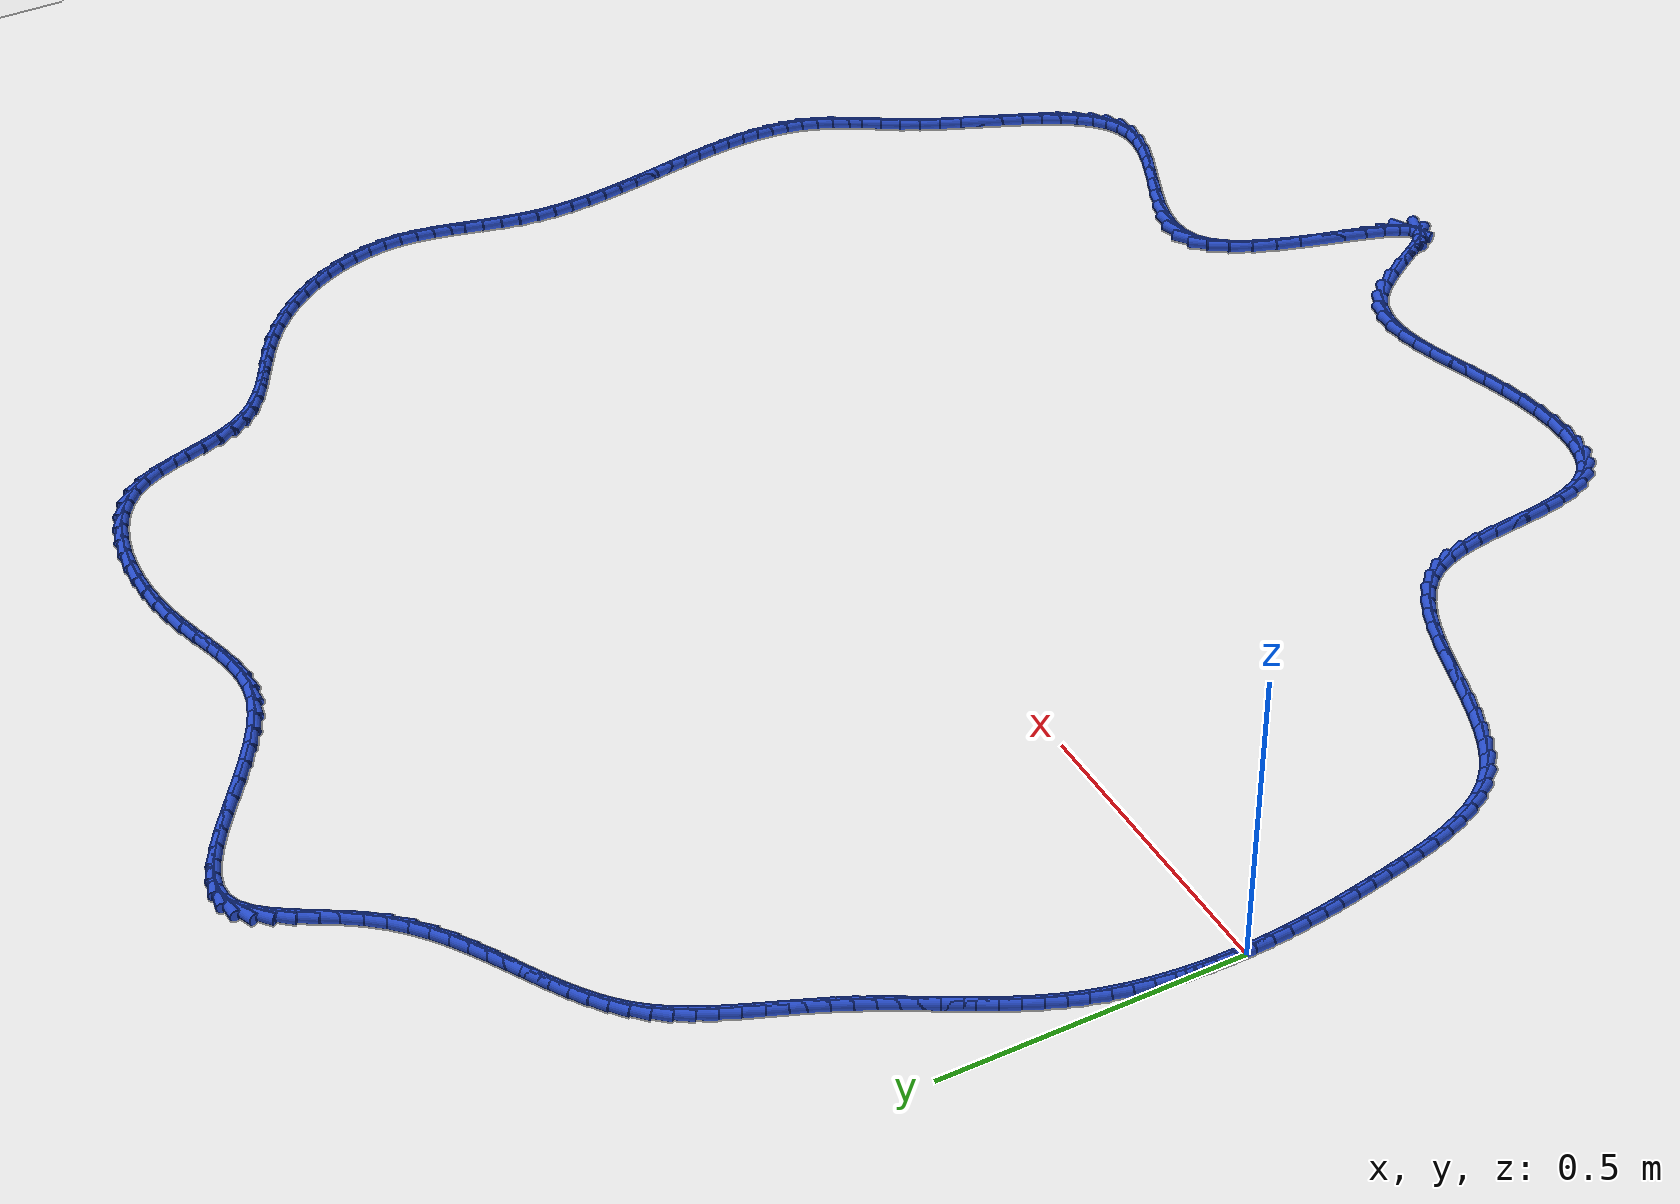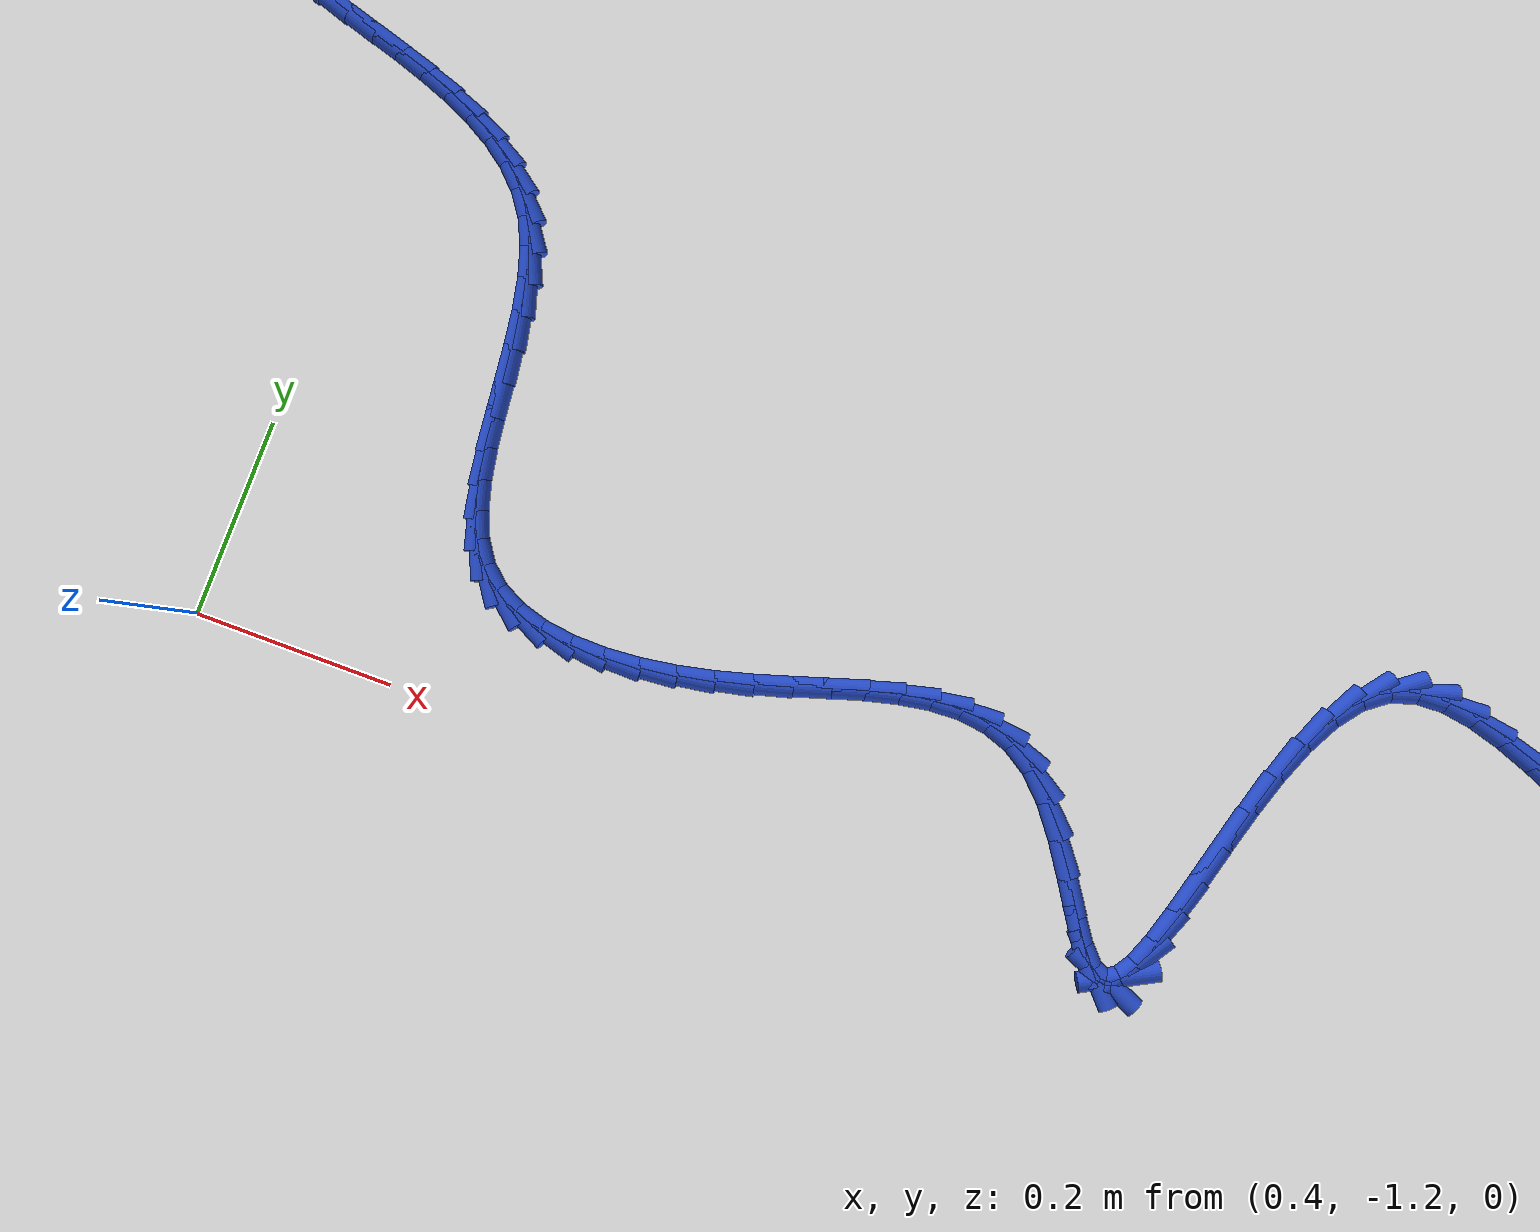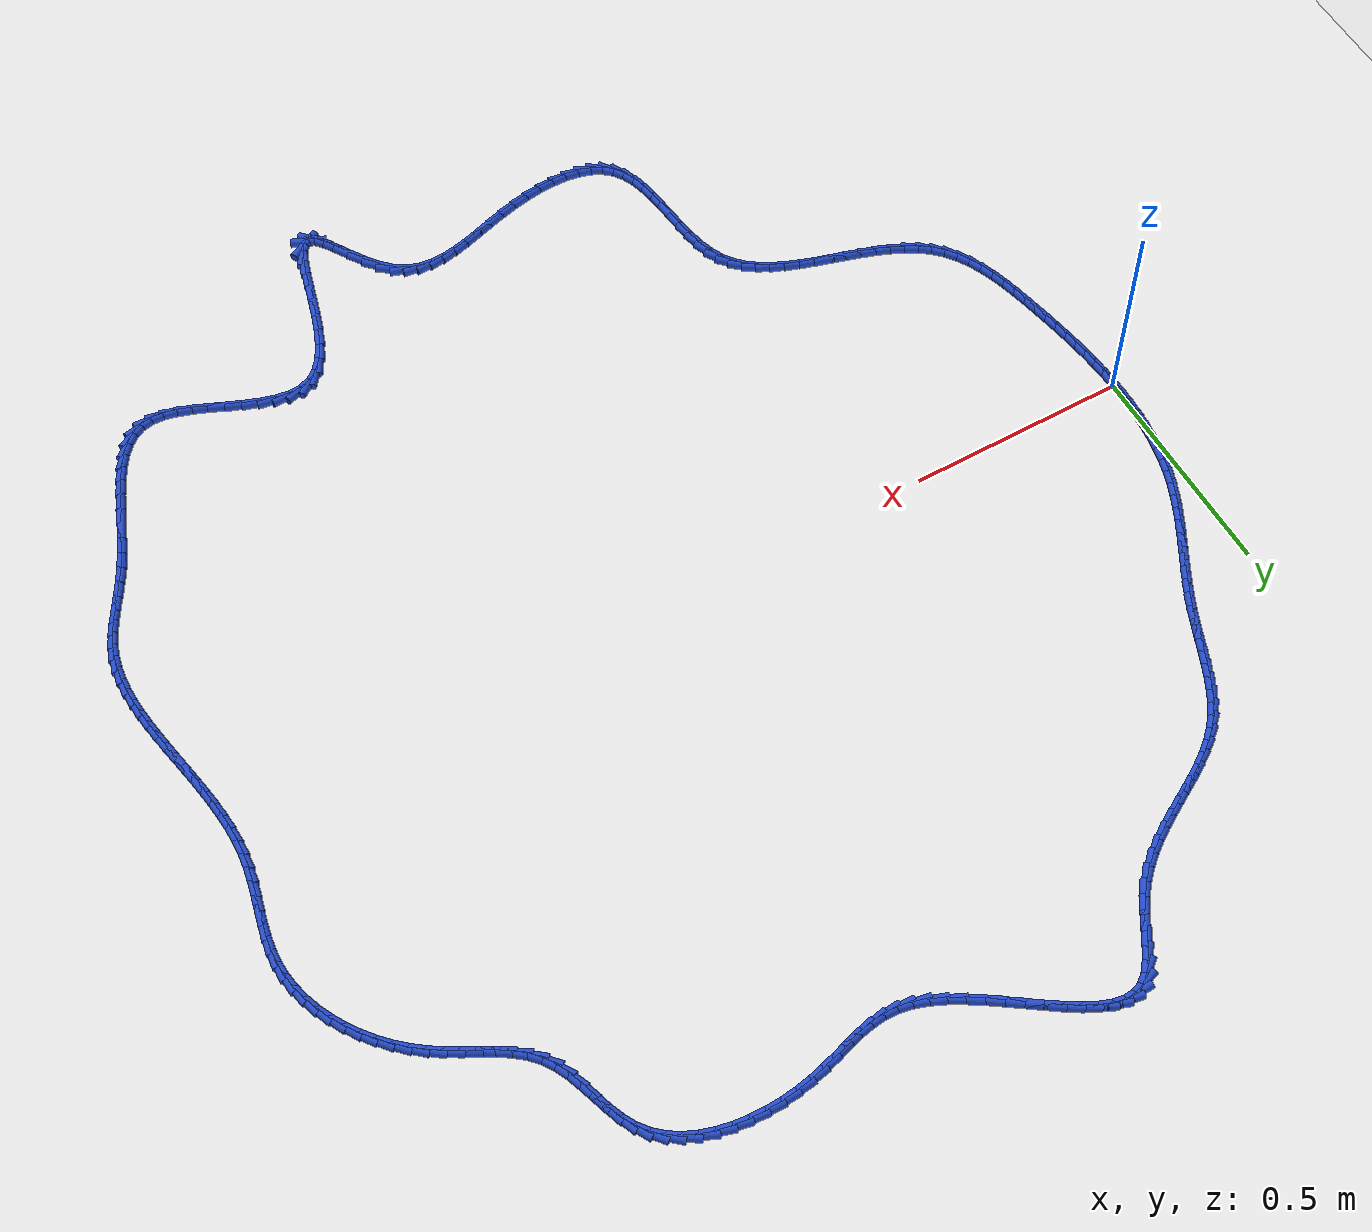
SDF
<sdf version="1.6">
 <world name="default">
  <light name="sun" type="directional">
   <pose>0 0 10 0 -0 0</pose>
   <diffuse>0.8 0.8 0.8 1</diffuse>
   <specular>0.2 0.2 0.2 1</specular>
   <attenuation>
    <range>1000</range>
    <constant>0.9</constant>
    <linear>0.01</linear>
    <quadratic>0.001</quadratic>
   </attenuation>
   <direction>-0.5 0.1 -0.9</direction>
  </light>
  <model name="ground_plane">
   <static>1</static>
   <link name="link">
    <collision name="collision">
     <geometry><plane><normal>0 0 1</normal><size>100 100</size></plane></geometry>
     <surface><friction><ode><mu>100</mu><mu2>50</mu2></ode></friction></surface>
    </collision>
    <visual name="visual">
     <cast_shadows>0</cast_shadows>
     <geometry><plane><normal>0 0 1</normal><size>100 100</size></plane></geometry>
     <material>
      <script><uri>file://media/materials/scripts/gazebo.material</uri><name>Gazebo/WhiteGlow</name></script>
     </material>
    </visual>
   </link>
  </model>
  <gravity>0 0 -9.8</gravity>
  <magnetic_field>6e-06 2.3e-05 -4.2e-05</magnetic_field>
  <atmosphere type="adiabatic"/>
  <physics name="default_physics" default="0" type="ode">
   <max_step_size>0.001</max_step_size>
   <real_time_factor>1</real_time_factor>
   <real_time_update_rate>1000</real_time_update_rate>
  </physics>
  <scene><ambient>0.4 0.4 0.4 1</ambient><background>0.7 0.7 0.7 1</background><shadows>1</shadows></scene>
  <spherical_coordinates>
   <surface_model>EARTH_WGS84</surface_model>
   <latitude_deg>0</latitude_deg>
   <longitude_deg>0</longitude_deg>
   <elevation>0</elevation>
   <heading_deg>0</heading_deg>
  </spherical_coordinates>
  <model name="line">
   <link name="link_0">
    <pose>1.6046192152785466e-17 4.163336342344337e-17 0.01 0 1.57 -1.5580116349688842</pose>
    <collision name="collision">
     <geometry><cylinder><radius>0.01</radius><length>0.08</length></cylinder></geometry>
    </collision>
    <visual name="visual">
     <material>
      <script><name>Gazebo/Blue</name><uri>file://media/materials/scripts/gazebo.material</uri></script>
     </material>
     <geometry><cylinder><radius>0.01</radius><length>0.08</length></cylinder></geometry>
    </visual>
   </link>
   <link name="link_1">
    <pose>-0.0004028578113779699 0.03150923524843937 0.01 0 1.57 1.5500419713608988</pose>
    <collision name="collision">
     <geometry><cylinder><radius>0.01</radius><length>0.08</length></cylinder></geometry>
    </collision>
    <visual name="visual">
     <material>
      <script><name>Gazebo/Blue</name><uri>file://media/materials/scripts/gazebo.material</uri></script>
     </material>
     <geometry><cylinder><radius>0.01</radius><length>0.08</length></cylinder></geometry>
    </visual>
   </link>
   <link name="link_2">
    <pose>0.0002549822827416621 0.06320116806231396 0.01 0 1.57 1.514115044767548</pose>
    <collision name="collision">
     <geometry><cylinder><radius>0.01</radius><length>0.08</length></cylinder></geometry>
    </collision>
    <visual name="visual">
     <material>
      <script><name>Gazebo/Blue</name><uri>file://media/materials/scripts/gazebo.material</uri></script>
     </material>
     <geometry><cylinder><radius>0.01</radius><length>0.08</length></cylinder></geometry>
    </visual>
   </link>
   <link name="link_3">
    <pose>0.002056200469738638 0.09494513616142236 0.01 0 1.57 1.475483794887779</pose>
    <collision name="collision">
     <geometry><cylinder><radius>0.01</radius><length>0.08</length></cylinder></geometry>
    </collision>
    <visual name="visual">
     <material>
      <script><name>Gazebo/Blue</name><uri>file://media/materials/scripts/gazebo.material</uri></script>
     </material>
     <geometry><cylinder><radius>0.01</radius><length>0.08</length></cylinder></geometry>
    </visual>
   </link>
   <link name="link_4">
    <pose>0.005083476936992688 0.126610477265563 0.01 0 1.57 1.4338159709183687</pose>
    <collision name="collision">
     <geometry><cylinder><radius>0.01</radius><length>0.08</length></cylinder></geometry>
    </collision>
    <visual name="visual">
     <material>
      <script><name>Gazebo/Blue</name><uri>file://media/materials/scripts/gazebo.material</uri></script>
     </material>
     <geometry><cylinder><radius>0.01</radius><length>0.08</length></cylinder></geometry>
    </visual>
   </link>
   <link name="link_5">
    <pose>0.00941949187188354 0.15806652909453447 0.01 0 1.57 1.3887672596449638</pose>
    <collision name="collision">
     <geometry><cylinder><radius>0.01</radius><length>0.08</length></cylinder></geometry>
    </collision>
    <visual name="visual">
     <material>
      <script><name>Gazebo/Blue</name><uri>file://media/materials/scripts/gazebo.material</uri></script>
     </material>
     <geometry><cylinder><radius>0.01</radius><length>0.08</length></cylinder></geometry>
    </visual>
   </link>
   <link name="link_6">
    <pose>0.015146925461790925 0.1891826293681352 0.01 0 1.57 1.3399892176934058</pose>
    <collision name="collision">
     <geometry><cylinder><radius>0.01</radius><length>0.08</length></cylinder></geometry>
    </collision>
    <visual name="visual">
     <material>
      <script><name>Gazebo/Blue</name><uri>file://media/materials/scripts/gazebo.material</uri></script>
     </material>
     <geometry><cylinder><radius>0.01</radius><length>0.08</length></cylinder></geometry>
    </visual>
   </link>
   <link name="link_7">
    <pose>0.02234845789409457 0.2198281158061638 0.01 0 1.57 1.287142812539969</pose>
    <collision name="collision">
     <geometry><cylinder><radius>0.01</radius><length>0.08</length></cylinder></geometry>
    </collision>
    <visual name="visual">
     <material>
      <script><name>Gazebo/Blue</name><uri>file://media/materials/scripts/gazebo.material</uri></script>
     </material>
     <geometry><cylinder><radius>0.01</radius><length>0.08</length></cylinder></geometry>
    </visual>
   </link>
   <link name="link_8">
    <pose>0.031106769356174187 0.2498723261284186 0.01 0 1.57 1.2306585767418146</pose>
    <collision name="collision">
     <geometry><cylinder><radius>0.01</radius><length>0.08</length></cylinder></geometry>
    </collision>
    <visual name="visual">
     <material>
      <script><name>Gazebo/Blue</name><uri>file://media/materials/scripts/gazebo.material</uri></script>
     </material>
     <geometry><cylinder><radius>0.01</radius><length>0.08</length></cylinder></geometry>
    </visual>
   </link>
   <link name="link_9">
    <pose>0.04148562995236788 0.27920009940941104 0.01 0 1.57 1.178217019345103</pose>
    <collision name="collision">
     <geometry><cylinder><radius>0.01</radius><length>0.08</length></cylinder></geometry>
    </collision>
    <visual name="visual">
     <material>
      <script><name>Gazebo/Blue</name><uri>file://media/materials/scripts/gazebo.material</uri></script>
     </material>
     <geometry><cylinder><radius>0.01</radius><length>0.08</length></cylinder></geometry>
    </visual>
   </link>
   <link name="link_10">
    <pose>0.053351953241081086 0.30785764594234605 0.01 0 1.57 1.1348469808931223</pose>
    <collision name="collision">
     <geometry><cylinder><radius>0.01</radius><length>0.08</length></cylinder></geometry>
    </collision>
    <visual name="visual">
     <material>
      <script><name>Gazebo/Blue</name><uri>file://media/materials/scripts/gazebo.material</uri></script>
     </material>
     <geometry><cylinder><radius>0.01</radius><length>0.08</length></cylinder></geometry>
    </visual>
   </link>
   <link name="link_11">
    <pose>0.06645576918653144 0.3359869901979562 0.01 0 1.57 1.1008944626769803</pose>
    <collision name="collision">
     <geometry><cylinder><radius>0.01</radius><length>0.08</length></cylinder></geometry>
    </collision>
    <visual name="visual">
     <material>
      <script><name>Gazebo/Blue</name><uri>file://media/materials/scripts/gazebo.material</uri></script>
     </material>
     <geometry><cylinder><radius>0.01</radius><length>0.08</length></cylinder></geometry>
    </visual>
   </link>
   <link name="link_12">
    <pose>0.08054556777313687 0.3637314190302788 0.01 0 1.57 1.076430242443896</pose>
    <collision name="collision">
     <geometry><cylinder><radius>0.01</radius><length>0.08</length></cylinder></geometry>
    </collision>
    <visual name="visual">
     <material>
      <script><name>Gazebo/Blue</name><uri>file://media/materials/scripts/gazebo.material</uri></script>
     </material>
     <geometry><cylinder><radius>0.01</radius><length>0.08</length></cylinder></geometry>
    </visual>
   </link>
   <link name="link_13">
    <pose>0.09536983898531506 0.39123421929335106 0.01 0 1.57 1.061399354472699</pose>
    <collision name="collision">
     <geometry><cylinder><radius>0.01</radius><length>0.08</length></cylinder></geometry>
    </collision>
    <visual name="visual">
     <material>
      <script><name>Gazebo/Blue</name><uri>file://media/materials/scripts/gazebo.material</uri></script>
     </material>
     <geometry><cylinder><radius>0.01</radius><length>0.08</length></cylinder></geometry>
    </visual>
   </link>
   <link name="link_14">
    <pose>0.11067707280748393 0.41863867784121034 0.01 0 1.57 1.055687970877207</pose>
    <collision name="collision">
     <geometry><cylinder><radius>0.01</radius><length>0.08</length></cylinder></geometry>
    </collision>
    <visual name="visual">
     <material>
      <script><name>Gazebo/Blue</name><uri>file://media/materials/scripts/gazebo.material</uri></script>
     </material>
     <geometry><cylinder><radius>0.01</radius><length>0.08</length></cylinder></geometry>
    </visual>
   </link>
   <link name="link_15">
    <pose>0.1262157592240613 0.44608808152789425 0.01 0 1.57 1.0591641786545154</pose>
    <collision name="collision">
     <geometry><cylinder><radius>0.01</radius><length>0.08</length></cylinder></geometry>
    </collision>
    <visual name="visual">
     <material>
      <script><name>Gazebo/Blue</name><uri>file://media/materials/scripts/gazebo.material</uri></script>
     </material>
     <geometry><cylinder><radius>0.01</radius><length>0.08</length></cylinder></geometry>
    </visual>
   </link>
   <link name="link_16">
    <pose>0.141734388219465 0.47372571720743983 0.01 0 1.57 1.071693252115393</pose>
    <collision name="collision">
     <geometry><cylinder><radius>0.01</radius><length>0.08</length></cylinder></geometry>
    </collision>
    <visual name="visual">
     <material>
      <script><name>Gazebo/Blue</name><uri>file://media/materials/scripts/gazebo.material</uri></script>
     </material>
     <geometry><cylinder><radius>0.01</radius><length>0.08</length></cylinder></geometry>
    </visual>
   </link>
   <link name="link_17">
    <pose>0.15698144977811287 0.5016948717338846 0.01 0 1.57 1.093129509462431</pose>
    <collision name="collision">
     <geometry><cylinder><radius>0.01</radius><length>0.08</length></cylinder></geometry>
    </collision>
    <visual name="visual">
     <material>
      <script><name>Gazebo/Blue</name><uri>file://media/materials/scripts/gazebo.material</uri></script>
     </material>
     <geometry><cylinder><radius>0.01</radius><length>0.08</length></cylinder></geometry>
    </visual>
   </link>
   <link name="link_18">
    <pose>0.1717054338844228 0.5301388319612659 0.01 0 1.57 1.1232820498886869</pose>
    <collision name="collision">
     <geometry><cylinder><radius>0.01</radius><length>0.08</length></cylinder></geometry>
    </collision>
    <visual name="visual">
     <material>
      <script><name>Gazebo/Blue</name><uri>file://media/materials/scripts/gazebo.material</uri></script>
     </material>
     <geometry><cylinder><radius>0.01</radius><length>0.08</length></cylinder></geometry>
    </visual>
   </link>
   <link name="link_19">
    <pose>0.18565496490613353 0.5592007794158209 0.01 0 1.57 1.1563778654326762</pose>
    <collision name="collision">
     <geometry><cylinder><radius>0.01</radius><length>0.08</length></cylinder></geometry>
    </collision>
    <visual name="visual">
     <material>
      <script><name>Gazebo/Blue</name><uri>file://media/materials/scripts/gazebo.material</uri></script>
     </material>
     <geometry><cylinder><radius>0.01</radius><length>0.08</length></cylinder></geometry>
    </visual>
   </link>
   <link name="link_20">
    <pose>0.1987239112239782 0.5889100553622971 0.01 0 1.57 1.1765437617916505</pose>
    <collision name="collision">
     <geometry><cylinder><radius>0.01</radius><length>0.08</length></cylinder></geometry>
    </collision>
    <visual name="visual">
     <material>
      <script><name>Gazebo/Blue</name><uri>file://media/materials/scripts/gazebo.material</uri></script>
     </material>
     <geometry><cylinder><radius>0.01</radius><length>0.08</length></cylinder></geometry>
    </visual>
   </link>
   <link name="link_21">
    <pose>0.21122796983377556 0.6189653775935705 0.01 0 1.57 1.1812873094814231</pose>
    <collision name="collision">
     <geometry><cylinder><radius>0.01</radius><length>0.08</length></cylinder></geometry>
    </collision>
    <visual name="visual">
     <material>
      <script><name>Gazebo/Blue</name><uri>file://media/materials/scripts/gazebo.material</uri></script>
     </material>
     <geometry><cylinder><radius>0.01</radius><length>0.08</length></cylinder></geometry>
    </visual>
   </link>
   <link name="link_22">
    <pose>0.22355898667686047 0.6490057794054344 0.01 0 1.57 1.1705714123214415</pose>
    <collision name="collision">
     <geometry><cylinder><radius>0.01</radius><length>0.08</length></cylinder></geometry>
    </collision>
    <visual name="visual">
     <material>
      <script><name>Gazebo/Blue</name><uri>file://media/materials/scripts/gazebo.material</uri></script>
     </material>
     <geometry><cylinder><radius>0.01</radius><length>0.08</length></cylinder></geometry>
    </visual>
   </link>
   <link name="link_23">
    <pose>0.23610880769456769 0.6786702940936831 0.01 0 1.57 1.1438384274842417</pose>
    <collision name="collision">
     <geometry><cylinder><radius>0.01</radius><length>0.08</length></cylinder></geometry>
    </collision>
    <visual name="visual">
     <material>
      <script><name>Gazebo/Blue</name><uri>file://media/materials/scripts/gazebo.material</uri></script>
     </material>
     <geometry><cylinder><radius>0.01</radius><length>0.08</length></cylinder></geometry>
    </visual>
   </link>
   <link name="link_24">
    <pose>0.2492692788282322 0.7075979549541104 0.01 0 1.57 1.1000437780483252</pose>
    <collision name="collision">
     <geometry><cylinder><radius>0.01</radius><length>0.08</length></cylinder></geometry>
    </collision>
    <visual name="visual">
     <material>
      <script><name>Gazebo/Blue</name><uri>file://media/materials/scripts/gazebo.material</uri></script>
     </material>
     <geometry><cylinder><radius>0.01</radius><length>0.08</length></cylinder></geometry>
    </visual>
   </link>
   <link name="link_25">
    <pose>0.2634322460191886 0.7354277952825098 0.01 0 1.57 1.037807565165716</pose>
    <collision name="collision">
     <geometry><cylinder><radius>0.01</radius><length>0.08</length></cylinder></geometry>
    </collision>
    <visual name="visual">
     <material>
      <script><name>Gazebo/Blue</name><uri>file://media/materials/scripts/gazebo.material</uri></script>
     </material>
     <geometry><cylinder><radius>0.01</radius><length>0.08</length></cylinder></geometry>
    </visual>
   </link>
   <link name="link_26">
    <pose>0.2789895552087718 0.7617988483746758 0.01 0 1.57 0.9557754795872594</pose>
    <collision name="collision">
     <geometry><cylinder><radius>0.01</radius><length>0.08</length></cylinder></geometry>
    </collision>
    <visual name="visual">
     <material>
      <script><name>Gazebo/Blue</name><uri>file://media/materials/scripts/gazebo.material</uri></script>
     </material>
     <geometry><cylinder><radius>0.01</radius><length>0.08</length></cylinder></geometry>
    </visual>
   </link>
   <link name="link_27">
    <pose>0.2963330523383165 0.7863501475264018 0.01 0 1.57 0.8540498385770475</pose>
    <collision name="collision">
     <geometry><cylinder><radius>0.01</radius><length>0.08</length></cylinder></geometry>
    </collision>
    <visual name="visual">
     <material>
      <script><name>Gazebo/Blue</name><uri>file://media/materials/scripts/gazebo.material</uri></script>
     </material>
     <geometry><cylinder><radius>0.01</radius><length>0.08</length></cylinder></geometry>
    </visual>
   </link>
   <link name="link_28">
    <pose>0.3158392205192975 0.8087368588711776 0.01 0 1.57 0.7508790296116303</pose>
    <collision name="collision">
     <geometry><cylinder><radius>0.01</radius><length>0.08</length></cylinder></geometry>
    </collision>
    <visual name="visual">
     <material>
      <script><name>Gazebo/Blue</name><uri>file://media/materials/scripts/gazebo.material</uri></script>
     </material>
     <geometry><cylinder><radius>0.01</radius><length>0.08</length></cylinder></geometry>
    </visual>
   </link>
   <link name="link_29">
    <pose>0.3375334818481241 0.8289828052567043 0.01 0 1.57 0.6656146132157014</pose>
    <collision name="collision">
     <geometry><cylinder><radius>0.01</radius><length>0.08</length></cylinder></geometry>
    </collision>
    <visual name="visual">
     <material>
      <script><name>Gazebo/Blue</name><uri>file://media/materials/scripts/gazebo.material</uri></script>
     </material>
     <geometry><cylinder><radius>0.01</radius><length>0.08</length></cylinder></geometry>
    </visual>
   </link>
   <link name="link_30">
    <pose>0.36109146166578243 0.8474791386186858 0.01 0 1.57 0.5998390443122779</pose>
    <collision name="collision">
     <geometry><cylinder><radius>0.01</radius><length>0.08</length></cylinder></geometry>
    </collision>
    <visual name="visual">
     <material>
      <script><name>Gazebo/Blue</name><uri>file://media/materials/scripts/gazebo.material</uri></script>
     </material>
     <geometry><cylinder><radius>0.01</radius><length>0.08</length></cylinder></geometry>
    </visual>
   </link>
   <link name="link_31">
    <pose>0.38617367533635816 0.8646328782041939 0.01 0 1.57 0.5531414395964439</pose>
    <collision name="collision">
     <geometry><cylinder><radius>0.01</radius><length>0.08</length></cylinder></geometry>
    </collision>
    <visual name="visual">
     <material>
      <script><name>Gazebo/Blue</name><uri>file://media/materials/scripts/gazebo.material</uri></script>
     </material>
     <geometry><cylinder><radius>0.01</radius><length>0.08</length></cylinder></geometry>
    </visual>
   </link>
   <link name="link_32">
    <pose>0.4124406382239377 0.8808510432603021 0.01 0 1.57 0.5246039540064308</pose>
    <collision name="collision">
     <geometry><cylinder><radius>0.01</radius><length>0.08</length></cylinder></geometry>
    </collision>
    <visual name="visual">
     <material>
      <script><name>Gazebo/Blue</name><uri>file://media/materials/scripts/gazebo.material</uri></script>
     </material>
     <geometry><cylinder><radius>0.01</radius><length>0.08</length></cylinder></geometry>
    </visual>
   </link>
   <link name="link_33">
    <pose>0.4395528656926066 0.8965406530340823 0.01 0 1.57 0.513295151443364</pose>
    <collision name="collision">
     <geometry><cylinder><radius>0.01</radius><length>0.08</length></cylinder></geometry>
    </collision>
    <visual name="visual">
     <material>
      <script><name>Gazebo/Blue</name><uri>file://media/materials/scripts/gazebo.material</uri></script>
     </material>
     <geometry><cylinder><radius>0.01</radius><length>0.08</length></cylinder></geometry>
    </visual>
   </link>
   <link name="link_34">
    <pose>0.4671708731064505 0.9121087267726075 0.01 0 1.57 0.5185167637893923</pose>
    <collision name="collision">
     <geometry><cylinder><radius>0.01</radius><length>0.08</length></cylinder></geometry>
    </collision>
    <visual name="visual">
     <material>
      <script><name>Gazebo/Blue</name><uri>file://media/materials/scripts/gazebo.material</uri></script>
     </material>
     <geometry><cylinder><radius>0.01</radius><length>0.08</length></cylinder></geometry>
    </visual>
   </link>
   <link name="link_35">
    <pose>0.4949551758295555 0.9279622837229498 0.01 0 1.57 0.5398705041773794</pose>
    <collision name="collision">
     <geometry><cylinder><radius>0.01</radius><length>0.08</length></cylinder></geometry>
    </collision>
    <visual name="visual">
     <material>
      <script><name>Gazebo/Blue</name><uri>file://media/materials/scripts/gazebo.material</uri></script>
     </material>
     <geometry><cylinder><radius>0.01</radius><length>0.08</length></cylinder></geometry>
    </visual>
   </link>
   <link name="link_36">
    <pose>0.5225662892260076 0.9445083431321827 0.01 0 1.57 0.5771944339568059</pose>
    <collision name="collision">
     <geometry><cylinder><radius>0.01</radius><length>0.08</length></cylinder></geometry>
    </collision>
    <visual name="visual">
     <material>
      <script><name>Gazebo/Blue</name><uri>file://media/materials/scripts/gazebo.material</uri></script>
     </material>
     <geometry><cylinder><radius>0.01</radius><length>0.08</length></cylinder></geometry>
    </visual>
   </link>
   <link name="link_37">
    <pose>0.5496647286598928 0.9621539242473788 0.01 0 1.57 0.6303872662842359</pose>
    <collision name="collision">
     <geometry><cylinder><radius>0.01</radius><length>0.08</length></cylinder></geometry>
    </collision>
    <visual name="visual">
     <material>
      <script><name>Gazebo/Blue</name><uri>file://media/materials/scripts/gazebo.material</uri></script>
     </material>
     <geometry><cylinder><radius>0.01</radius><length>0.08</length></cylinder></geometry>
    </visual>
   </link>
   <link name="link_38">
    <pose>0.5759110094952964 0.9813060463156099 0.01 0 1.57 0.6991226731353587</pose>
    <collision name="collision">
     <geometry><cylinder><radius>0.01</radius><length>0.08</length></cylinder></geometry>
    </collision>
    <visual name="visual">
     <material>
      <script><name>Gazebo/Blue</name><uri>file://media/materials/scripts/gazebo.material</uri></script>
     </material>
     <geometry><cylinder><radius>0.01</radius><length>0.08</length></cylinder></geometry>
    </visual>
   </link>
   <link name="link_39">
    <pose>0.6009656470963051 1.00237172858395 0.01 0 1.57 0.7824723844110075</pose>
    <collision name="collision">
     <geometry><cylinder><radius>0.01</radius><length>0.08</length></cylinder></geometry>
    </collision>
    <visual name="visual">
     <material>
      <script><name>Gazebo/Blue</name><uri>file://media/materials/scripts/gazebo.material</uri></script>
     </material>
     <geometry><cylinder><radius>0.01</radius><length>0.08</length></cylinder></geometry>
    </visual>
   </link>
   <link name="link_40">
    <pose>0.6244891568270039 1.0257579902994698 0.01 0 1.57 0.8784894327376682</pose>
    <collision name="collision">
     <geometry><cylinder><radius>0.01</radius><length>0.08</length></cylinder></geometry>
    </collision>
    <visual name="visual">
     <material>
      <script><name>Gazebo/Blue</name><uri>file://media/materials/scripts/gazebo.material</uri></script>
     </material>
     <geometry><cylinder><radius>0.01</radius><length>0.08</length></cylinder></geometry>
    </visual>
   </link>
   <link name="link_41">
    <pose>0.646142512180271 1.0518708529762404 0.01 0 1.57 0.9693395909488022</pose>
    <collision name="collision">
     <geometry><cylinder><radius>0.01</radius><length>0.08</length></cylinder></geometry>
    </collision>
    <visual name="visual">
     <material>
      <script><name>Gazebo/Blue</name><uri>file://media/materials/scripts/gazebo.material</uri></script>
     </material>
     <geometry><cylinder><radius>0.01</radius><length>0.08</length></cylinder></geometry>
    </visual>
   </link>
   <link name="link_42">
    <pose>0.6658377659725696 1.080569526549648 0.01 0 1.57 1.0180753666438616</pose>
    <collision name="collision">
     <geometry><cylinder><radius>0.01</radius><length>0.08</length></cylinder></geometry>
    </collision>
    <visual name="visual">
     <material>
      <script><name>Gazebo/Blue</name><uri>file://media/materials/scripts/gazebo.material</uri></script>
     </material>
     <geometry><cylinder><radius>0.01</radius><length>0.08</length></cylinder></geometry>
    </visual>
   </link>
   <link name="link_43">
    <pose>0.6841534967865807 1.1102616318666245 0.01 0 1.57 1.0224853365592925</pose>
    <collision name="collision">
     <geometry><cylinder><radius>0.01</radius><length>0.08</length></cylinder></geometry>
    </collision>
    <visual name="visual">
     <material>
      <script><name>Gazebo/Blue</name><uri>file://media/materials/scripts/gazebo.material</uri></script>
     </material>
     <geometry><cylinder><radius>0.01</radius><length>0.08</length></cylinder></geometry>
    </visual>
   </link>
   <link name="link_44">
    <pose>0.7017776478181831 1.139116610716018 0.01 0 1.57 0.9785148167061688</pose>
    <collision name="collision">
     <geometry><cylinder><radius>0.01</radius><length>0.08</length></cylinder></geometry>
    </collision>
    <visual name="visual">
     <material>
      <script><name>Gazebo/Blue</name><uri>file://media/materials/scripts/gazebo.material</uri></script>
     </material>
     <geometry><cylinder><radius>0.01</radius><length>0.08</length></cylinder></geometry>
    </visual>
   </link>
   <link name="link_45">
    <pose>0.7193981622632561 1.1653039048866785 0.01 0 1.57 0.8698157792936966</pose>
    <collision name="collision">
     <geometry><cylinder><radius>0.01</radius><length>0.08</length></cylinder></geometry>
    </collision>
    <visual name="visual">
     <material>
      <script><name>Gazebo/Blue</name><uri>file://media/materials/scripts/gazebo.material</uri></script>
     </material>
     <geometry><cylinder><radius>0.01</radius><length>0.08</length></cylinder></geometry>
    </visual>
   </link>
   <link name="link_46">
    <pose>0.7377029833176794 1.186992956167456 0.01 0 1.57 0.6628381391110635</pose>
    <collision name="collision">
     <geometry><cylinder><radius>0.01</radius><length>0.08</length></cylinder></geometry>
    </collision>
    <visual name="visual">
     <material>
      <script><name>Gazebo/Blue</name><uri>file://media/materials/scripts/gazebo.material</uri></script>
     </material>
     <geometry><cylinder><radius>0.01</radius><length>0.08</length></cylinder></geometry>
    </visual>
   </link>
   <link name="link_47">
    <pose>0.7573798263681768 1.202353932111893 0.01 0 1.57 0.3489873035562371</pose>
    <collision name="collision">
     <geometry><cylinder><radius>0.01</radius><length>0.08</length></cylinder></geometry>
    </collision>
    <visual name="visual">
     <material>
      <script><name>Gazebo/Blue</name><uri>file://media/materials/scripts/gazebo.material</uri></script>
     </material>
     <geometry><cylinder><radius>0.01</radius><length>0.08</length></cylinder></geometry>
    </visual>
   </link>
   <link name="link_48">
    <pose>0.7789173867754706 1.210191047258453 0.01 0 1.57 0.03909313656867497</pose>
    <collision name="collision">
     <geometry><cylinder><radius>0.01</radius><length>0.08</length></cylinder></geometry>
    </collision>
    <visual name="visual">
     <material>
      <script><name>Gazebo/Blue</name><uri>file://media/materials/scripts/gazebo.material</uri></script>
     </material>
     <geometry><cylinder><radius>0.01</radius><length>0.08</length></cylinder></geometry>
    </visual>
   </link>
   <link name="link_49">
    <pose>0.8022409963792325 1.2111033050877587 0.01 0 1.57 -0.2016733695533999</pose>
    <collision name="collision">
     <geometry><cylinder><radius>0.01</radius><length>0.08</length></cylinder></geometry>
    </collision>
    <visual name="visual">
     <material>
      <script><name>Gazebo/Blue</name><uri>file://media/materials/scripts/gazebo.material</uri></script>
     </material>
     <geometry><cylinder><radius>0.01</radius><length>0.08</length></cylinder></geometry>
    </visual>
   </link>
   <link name="link_50">
    <pose>0.827176998672758 1.2060050706238077 0.01 0 1.57 -0.3688318774358598</pose>
    <collision name="collision">
     <geometry><cylinder><radius>0.01</radius><length>0.08</length></cylinder></geometry>
    </collision>
    <visual name="visual">
     <material>
      <script><name>Gazebo/Blue</name><uri>file://media/materials/scripts/gazebo.material</uri></script>
     </material>
     <geometry><cylinder><radius>0.01</radius><length>0.08</length></cylinder></geometry>
    </visual>
   </link>
   <link name="link_51">
    <pose>0.8535517371493413 1.1958107088905978 0.01 0 1.57 -0.4796166435442377</pose>
    <collision name="collision">
     <geometry><cylinder><radius>0.01</radius><length>0.08</length></cylinder></geometry>
    </collision>
    <visual name="visual">
     <material>
      <script><name>Gazebo/Blue</name><uri>file://media/materials/scripts/gazebo.material</uri></script>
     </material>
     <geometry><cylinder><radius>0.01</radius><length>0.08</length></cylinder></geometry>
    </visual>
   </link>
   <link name="link_52">
    <pose>0.8811915553022793 1.1814345849121275 0.01 0 1.57 -0.5507142445711828</pose>
    <collision name="collision">
     <geometry><cylinder><radius>0.01</radius><length>0.08</length></cylinder></geometry>
    </collision>
    <visual name="visual">
     <material>
      <script><name>Gazebo/Blue</name><uri>file://media/materials/scripts/gazebo.material</uri></script>
     </material>
     <geometry><cylinder><radius>0.01</radius><length>0.08</length></cylinder></geometry>
    </visual>
   </link>
   <link name="link_53">
    <pose>0.9099227966248652 1.1637910637123934 0.01 0 1.57 -0.5933666246820535</pose>
    <collision name="collision">
     <geometry><cylinder><radius>0.01</radius><length>0.08</length></cylinder></geometry>
    </collision>
    <visual name="visual">
     <material>
      <script><name>Gazebo/Blue</name><uri>file://media/materials/scripts/gazebo.material</uri></script>
     </material>
     <geometry><cylinder><radius>0.01</radius><length>0.08</length></cylinder></geometry>
    </visual>
   </link>
   <link name="link_54">
    <pose>0.9395718046103957 1.1437945103153937 0.01 0 1.57 -0.614251185983366</pose>
    <collision name="collision">
     <geometry><cylinder><radius>0.01</radius><length>0.08</length></cylinder></geometry>
    </collision>
    <visual name="visual">
     <material>
      <script><name>Gazebo/Blue</name><uri>file://media/materials/scripts/gazebo.material</uri></script>
     </material>
     <geometry><cylinder><radius>0.01</radius><length>0.08</length></cylinder></geometry>
    </visual>
   </link>
   <link name="link_55">
    <pose>0.969964922752165 1.1223592897451264 0.01 0 1.57 -0.6168771979844756</pose>
    <collision name="collision">
     <geometry><cylinder><radius>0.01</radius><length>0.08</length></cylinder></geometry>
    </collision>
    <visual name="visual">
     <material>
      <script><name>Gazebo/Blue</name><uri>file://media/materials/scripts/gazebo.material</uri></script>
     </material>
     <geometry><cylinder><radius>0.01</radius><length>0.08</length></cylinder></geometry>
    </visual>
   </link>
   <link name="link_56">
    <pose>1.0009284945434687 1.1003997670255883 0.01 0 1.57 -0.6024866604351783</pose>
    <collision name="collision">
     <geometry><cylinder><radius>0.01</radius><length>0.08</length></cylinder></geometry>
    </collision>
    <visual name="visual">
     <material>
      <script><name>Gazebo/Blue</name><uri>file://media/materials/scripts/gazebo.material</uri></script>
     </material>
     <geometry><cylinder><radius>0.01</radius><length>0.08</length></cylinder></geometry>
    </visual>
   </link>
   <link name="link_57">
    <pose>1.0322888634776015 1.0788303071807774 0.01 0 1.57 -0.5704710401238443</pose>
    <collision name="collision">
     <geometry><cylinder><radius>0.01</radius><length>0.08</length></cylinder></geometry>
    </collision>
    <visual name="visual">
     <material>
      <script><name>Gazebo/Blue</name><uri>file://media/materials/scripts/gazebo.material</uri></script>
     </material>
     <geometry><cylinder><radius>0.01</radius><length>0.08</length></cylinder></geometry>
    </visual>
   </link>
   <link name="link_58">
    <pose>1.0638723730478594 1.0585652752346917 0.01 0 1.57 -0.5184366785800043</pose>
    <collision name="collision">
     <geometry><cylinder><radius>0.01</radius><length>0.08</length></cylinder></geometry>
    </collision>
    <visual name="visual">
     <material>
      <script><name>Gazebo/Blue</name><uri>file://media/materials/scripts/gazebo.material</uri></script>
     </material>
     <geometry><cylinder><radius>0.01</radius><length>0.08</length></cylinder></geometry>
    </visual>
   </link>
   <link name="link_59">
    <pose>1.095505366747537 1.0405190362113288 0.01 0 1.57 -0.4420592331321843</pose>
    <collision name="collision">
     <geometry><cylinder><radius>0.01</radius><length>0.08</length></cylinder></geometry>
    </collision>
    <visual name="visual">
     <material>
      <script><name>Gazebo/Blue</name><uri>file://media/materials/scripts/gazebo.material</uri></script>
     </material>
     <geometry><cylinder><radius>0.01</radius><length>0.08</length></cylinder></geometry>
    </visual>
   </link>
   <link name="link_60">
    <pose>1.1270141880699294 1.0256059551346866 0.01 0 1.57 -0.33501007679071076</pose>
    <collision name="collision">
     <geometry><cylinder><radius>0.01</radius><length>0.08</length></cylinder></geometry>
    </collision>
    <visual name="visual">
     <material>
      <script><name>Gazebo/Blue</name><uri>file://media/materials/scripts/gazebo.material</uri></script>
     </material>
     <geometry><cylinder><radius>0.01</radius><length>0.08</length></cylinder></geometry>
    </visual>
   </link>
   <link name="link_61">
    <pose>1.1582251805083317 1.0147403970287618 0.01 0 1.57 -0.19038023095462722</pose>
    <collision name="collision">
     <geometry><cylinder><radius>0.01</radius><length>0.08</length></cylinder></geometry>
    </collision>
    <visual name="visual">
     <material>
      <script><name>Gazebo/Blue</name><uri>file://media/materials/scripts/gazebo.material</uri></script>
     </material>
     <geometry><cylinder><radius>0.01</radius><length>0.08</length></cylinder></geometry>
    </visual>
   </link>
   <link name="link_62">
    <pose>1.1889694323852427 1.0088155443246916 0.01 0 1.57 -0.029763182578734455</pose>
    <collision name="collision">
     <geometry><cylinder><radius>0.01</radius><length>0.08</length></cylinder></geometry>
    </collision>
    <visual name="visual">
     <material>
      <script><name>Gazebo/Blue</name><uri>file://media/materials/scripts/gazebo.material</uri></script>
     </material>
     <geometry><cylinder><radius>0.01</radius><length>0.08</length></cylinder></geometry>
    </visual>
   </link>
   <link name="link_63">
    <pose>1.219259656298973 1.007913744558719 0.01 0 1.57 0.104577634921689</pose>
    <collision name="collision">
     <geometry><cylinder><radius>0.01</radius><length>0.08</length></cylinder></geometry>
    </collision>
    <visual name="visual">
     <material>
      <script><name>Gazebo/Blue</name><uri>file://media/materials/scripts/gazebo.material</uri></script>
     </material>
     <geometry><cylinder><radius>0.01</radius><length>0.08</length></cylinder></geometry>
    </visual>
   </link>
   <link name="link_64">
    <pose>1.2493428763923315 1.0110712958020205 0.01 0 1.57 0.20237610220196295</pose>
    <collision name="collision">
     <geometry><cylinder><radius>0.01</radius><length>0.08</length></cylinder></geometry>
    </collision>
    <visual name="visual">
     <material>
      <script><name>Gazebo/Blue</name><uri>file://media/materials/scripts/gazebo.material</uri></script>
     </material>
     <geometry><cylinder><radius>0.01</radius><length>0.08</length></cylinder></geometry>
    </visual>
   </link>
   <link name="link_65">
    <pose>1.2794816138638017 1.0172553117975678 0.01 0 1.57 0.2623116999090898</pose>
    <collision name="collision">
     <geometry><cylinder><radius>0.01</radius><length>0.08</length></cylinder></geometry>
    </collision>
    <visual name="visual">
     <material>
      <script><name>Gazebo/Blue</name><uri>file://media/materials/scripts/gazebo.material</uri></script>
     </material>
     <geometry><cylinder><radius>0.01</radius><length>0.08</length></cylinder></geometry>
    </visual>
   </link>
   <link name="link_66">
    <pose>1.3099383899118666 1.0254329062883318 0.01 0 1.57 0.2863378324115038</pose>
    <collision name="collision">
     <geometry><cylinder><radius>0.01</radius><length>0.08</length></cylinder></geometry>
    </collision>
    <visual name="visual">
     <material>
      <script><name>Gazebo/Blue</name><uri>file://media/materials/scripts/gazebo.material</uri></script>
     </material>
     <geometry><cylinder><radius>0.01</radius><length>0.08</length></cylinder></geometry>
    </visual>
   </link>
   <link name="link_67">
    <pose>1.340975725735008 1.0345711930172836 0.01 0 1.57 0.2770638922318361</pose>
    <collision name="collision">
     <geometry><cylinder><radius>0.01</radius><length>0.08</length></cylinder></geometry>
    </collision>
    <visual name="visual">
     <material>
      <script><name>Gazebo/Blue</name><uri>file://media/materials/scripts/gazebo.material</uri></script>
     </material>
     <geometry><cylinder><radius>0.01</radius><length>0.08</length></cylinder></geometry>
    </visual>
   </link>
   <link name="link_68">
    <pose>1.3728561425317098 1.0436372857273948 0.01 0 1.57 0.2368164613707582</pose>
    <collision name="collision">
     <geometry><cylinder><radius>0.01</radius><length>0.08</length></cylinder></geometry>
    </collision>
    <visual name="visual">
     <material>
      <script><name>Gazebo/Blue</name><uri>file://media/materials/scripts/gazebo.material</uri></script>
     </material>
     <geometry><cylinder><radius>0.01</radius><length>0.08</length></cylinder></geometry>
    </visual>
   </link>
   <link name="link_69">
    <pose>1.4058421595792607 1.0515983002713378 0.01 0 1.57 0.17305006333005546</pose>
    <collision name="collision">
     <geometry><cylinder><radius>0.01</radius><length>0.08</length></cylinder></geometry>
    </collision>
    <visual name="visual">
     <material>
      <script><name>Gazebo/Blue</name><uri>file://media/materials/scripts/gazebo.material</uri></script>
     </material>
     <geometry><cylinder><radius>0.01</radius><length>0.08</length></cylinder></geometry>
    </visual>
   </link>
   <link name="link_70">
    <pose>1.4400533205312338 1.0575783569273383 0.01 0 1.57 0.10544905646195034</pose>
    <collision name="collision">
     <geometry><cylinder><radius>0.01</radius><length>0.08</length></cylinder></geometry>
    </collision>
    <visual name="visual">
     <material>
      <script><name>Gazebo/Blue</name><uri>file://media/materials/scripts/gazebo.material</uri></script>
     </material>
     <geometry><cylinder><radius>0.01</radius><length>0.08</length></cylinder></geometry>
    </visual>
   </link>
   <link name="link_71">
    <pose>1.4750775320953884 1.0612853772616262 0.01 0 1.57 0.0361743263684197</pose>
    <collision name="collision">
     <geometry><cylinder><radius>0.01</radius><length>0.08</length></cylinder></geometry>
    </collision>
    <visual name="visual">
     <material>
      <script><name>Gazebo/Blue</name><uri>file://media/materials/scripts/gazebo.material</uri></script>
     </material>
     <geometry><cylinder><radius>0.01</radius><length>0.08</length></cylinder></geometry>
    </visual>
   </link>
   <link name="link_72">
    <pose>1.5103791586795463 1.062562947139907 0.01 0 1.57 -0.03731621830174317</pose>
    <collision name="collision">
     <geometry><cylinder><radius>0.01</radius><length>0.08</length></cylinder></geometry>
    </collision>
    <visual name="visual">
     <material>
      <script><name>Gazebo/Blue</name><uri>file://media/materials/scripts/gazebo.material</uri></script>
     </material>
     <geometry><cylinder><radius>0.01</radius><length>0.08</length></cylinder></geometry>
    </visual>
   </link>
   <link name="link_73">
    <pose>1.5454225646915274 1.061254652427885 0.01 0 1.57 -0.1177196578502447</pose>
    <collision name="collision">
     <geometry><cylinder><radius>0.01</radius><length>0.08</length></cylinder></geometry>
    </collision>
    <visual name="visual">
     <material>
      <script><name>Gazebo/Blue</name><uri>file://media/materials/scripts/gazebo.material</uri></script>
     </material>
     <geometry><cylinder><radius>0.01</radius><length>0.08</length></cylinder></geometry>
    </visual>
   </link>
   <link name="link_74">
    <pose>1.5796721145391537 1.0572040789912653 0.01 0 1.57 -0.20804090591801241</pose>
    <collision name="collision">
     <geometry><cylinder><radius>0.01</radius><length>0.08</length></cylinder></geometry>
    </collision>
    <visual name="visual">
     <material>
      <script><name>Gazebo/Blue</name><uri>file://media/materials/scripts/gazebo.material</uri></script>
     </material>
     <geometry><cylinder><radius>0.01</radius><length>0.08</length></cylinder></geometry>
    </visual>
   </link>
   <link name="link_75">
    <pose>1.6125921726302448 1.0502548126957534 0.01 0 1.57 -0.31165281383982457</pose>
    <collision name="collision">
     <geometry><cylinder><radius>0.01</radius><length>0.08</length></cylinder></geometry>
    </collision>
    <visual name="visual">
     <material>
      <script><name>Gazebo/Blue</name><uri>file://media/materials/scripts/gazebo.material</uri></script>
     </material>
     <geometry><cylinder><radius>0.01</radius><length>0.08</length></cylinder></geometry>
    </visual>
   </link>
   <link name="link_76">
    <pose>1.6436471033726219 1.0402504394070535 0.01 0 1.57 -0.4321457580533304</pose>
    <collision name="collision">
     <geometry><cylinder><radius>0.01</radius><length>0.08</length></cylinder></geometry>
    </collision>
    <visual name="visual">
     <material>
      <script><name>Gazebo/Blue</name><uri>file://media/materials/scripts/gazebo.material</uri></script>
     </material>
     <geometry><cylinder><radius>0.01</radius><length>0.08</length></cylinder></geometry>
    </visual>
   </link>
   <link name="link_77">
    <pose>1.6723012711741059 1.0270345449908709 0.01 0 1.57 -0.5727387896171474</pose>
    <collision name="collision">
     <geometry><cylinder><radius>0.01</radius><length>0.08</length></cylinder></geometry>
    </collision>
    <visual name="visual">
     <material>
      <script><name>Gazebo/Blue</name><uri>file://media/materials/scripts/gazebo.material</uri></script>
     </material>
     <geometry><cylinder><radius>0.01</radius><length>0.08</length></cylinder></geometry>
    </visual>
   </link>
   <link name="link_78">
    <pose>1.6980190404425184 1.0104507153129099 0.01 0 1.57 -0.7349720336584797</pose>
    <collision name="collision">
     <geometry><cylinder><radius>0.01</radius><length>0.08</length></cylinder></geometry>
    </collision>
    <visual name="visual">
     <material>
      <script><name>Gazebo/Blue</name><uri>file://media/materials/scripts/gazebo.material</uri></script>
     </material>
     <geometry><cylinder><radius>0.01</radius><length>0.08</length></cylinder></geometry>
    </visual>
   </link>
   <link name="link_79">
    <pose>1.7202647755856781 0.990342536238876 0.01 0 1.57 -0.9164704038280731</pose>
    <collision name="collision">
     <geometry><cylinder><radius>0.01</radius><length>0.08</length></cylinder></geometry>
    </collision>
    <visual name="visual">
     <material>
      <script><name>Gazebo/Blue</name><uri>file://media/materials/scripts/gazebo.material</uri></script>
     </material>
     <geometry><cylinder><radius>0.01</radius><length>0.08</length></cylinder></geometry>
    </visual>
   </link>
   <link name="link_80">
    <pose>1.7385089057036103 0.9665578266056106 0.01 0 1.57 -1.086791762393636</pose>
    <collision name="collision">
     <geometry><cylinder><radius>0.01</radius><length>0.08</length></cylinder></geometry>
    </collision>
    <visual name="visual">
     <material>
      <script><name>Gazebo/Blue</name><uri>file://media/materials/scripts/gazebo.material</uri></script>
     </material>
     <geometry><cylinder><radius>0.01</radius><length>0.08</length></cylinder></geometry>
    </visual>
   </link>
   <link name="link_81">
    <pose>1.7528098469880362 0.93935480239868 0.01 0 1.57 -1.2007898940351998</pose>
    <collision name="collision">
     <geometry><cylinder><radius>0.01</radius><length>0.08</length></cylinder></geometry>
    </collision>
    <visual name="visual">
     <material>
      <script><name>Gazebo/Blue</name><uri>file://media/materials/scripts/gazebo.material</uri></script>
     </material>
     <geometry><cylinder><radius>0.01</radius><length>0.08</length></cylinder></geometry>
    </visual>
   </link>
   <link name="link_82">
    <pose>1.7642968973734725 0.9097391225663795 0.01 0 1.57 -1.2606755758297927</pose>
    <collision name="collision">
     <geometry><cylinder><radius>0.01</radius><length>0.08</length></cylinder></geometry>
    </collision>
    <visual name="visual">
     <material>
      <script><name>Gazebo/Blue</name><uri>file://media/materials/scripts/gazebo.material</uri></script>
     </material>
     <geometry><cylinder><radius>0.01</radius><length>0.08</length></cylinder></geometry>
    </visual>
   </link>
   <link name="link_83">
    <pose>1.7742130206488198 0.8787957813744038 0.01 0 1.57 -1.272518125706769</pose>
    <collision name="collision">
     <geometry><cylinder><radius>0.01</radius><length>0.08</length></cylinder></geometry>
    </collision>
    <visual name="visual">
     <material>
      <script><name>Gazebo/Blue</name><uri>file://media/materials/scripts/gazebo.material</uri></script>
     </material>
     <geometry><cylinder><radius>0.01</radius><length>0.08</length></cylinder></geometry>
    </visual>
   </link>
   <link name="link_84">
    <pose>1.7838011806029819 0.8476097730884484 0.01 0 1.57 -1.2375644303284148</pose>
    <collision name="collision">
     <geometry><cylinder><radius>0.01</radius><length>0.08</length></cylinder></geometry>
    </collision>
    <visual name="visual">
     <material>
      <script><name>Gazebo/Blue</name><uri>file://media/materials/scripts/gazebo.material</uri></script>
     </material>
     <geometry><cylinder><radius>0.01</radius><length>0.08</length></cylinder></geometry>
    </visual>
   </link>
   <link name="link_85">
    <pose>1.7943043410248594 0.8172660919742074 0.01 0 1.57 -1.1516428490568216</pose>
    <collision name="collision">
     <geometry><cylinder><radius>0.01</radius><length>0.08</length></cylinder></geometry>
    </collision>
    <visual name="visual">
     <material>
      <script><name>Gazebo/Blue</name><uri>file://media/materials/scripts/gazebo.material</uri></script>
     </material>
     <geometry><cylinder><radius>0.01</radius><length>0.08</length></cylinder></geometry>
    </visual>
   </link>
   <link name="link_86">
    <pose>1.8069654657033543 0.7888497322973772 0.01 0 1.57 -1.0072085564155473</pose>
    <collision name="collision">
     <geometry><cylinder><radius>0.01</radius><length>0.08</length></cylinder></geometry>
    </collision>
    <visual name="visual">
     <material>
      <script><name>Gazebo/Blue</name><uri>file://media/materials/scripts/gazebo.material</uri></script>
     </material>
     <geometry><cylinder><radius>0.01</radius><length>0.08</length></cylinder></geometry>
    </visual>
   </link>
   <link name="link_87">
    <pose>1.8230226722200138 0.7634411045453814 0.01 0 1.57 -0.8298793850657311</pose>
    <collision name="collision">
     <geometry><cylinder><radius>0.01</radius><length>0.08</length></cylinder></geometry>
    </collision>
    <visual name="visual">
     <material>
      <script><name>Gazebo/Blue</name><uri>file://media/materials/scripts/gazebo.material</uri></script>
     </material>
     <geometry><cylinder><radius>0.01</radius><length>0.08</length></cylinder></geometry>
    </visual>
   </link>
   <link name="link_88">
    <pose>1.843077153402812 0.7415181848416587 0.01 0 1.57 -0.6862522929552971</pose>
    <collision name="collision">
     <geometry><cylinder><radius>0.01</radius><length>0.08</length></cylinder></geometry>
    </collision>
    <visual name="visual">
     <material>
      <script><name>Gazebo/Blue</name><uri>file://media/materials/scripts/gazebo.material</uri></script>
     </material>
     <geometry><cylinder><radius>0.01</radius><length>0.08</length></cylinder></geometry>
    </visual>
   </link>
   <link name="link_89">
    <pose>1.8664649429638493 0.7223623003757843 0.01 0 1.57 -0.5873866066985317</pose>
    <collision name="collision">
     <geometry><cylinder><radius>0.01</radius><length>0.08</length></cylinder></geometry>
    </collision>
    <visual name="visual">
     <material>
      <script><name>Gazebo/Blue</name><uri>file://media/materials/scripts/gazebo.material</uri></script>
     </material>
     <geometry><cylinder><radius>0.01</radius><length>0.08</length></cylinder></geometry>
    </visual>
   </link>
   <link name="link_90">
    <pose>1.8923727076621224 0.7051134998191315 0.01 0 1.57 -0.5305906490828892</pose>
    <collision name="collision">
     <geometry><cylinder><radius>0.01</radius><length>0.08</length></cylinder></geometry>
    </collision>
    <visual name="visual">
     <material>
      <script><name>Gazebo/Blue</name><uri>file://media/materials/scripts/gazebo.material</uri></script>
     </material>
     <geometry><cylinder><radius>0.01</radius><length>0.08</length></cylinder></geometry>
    </visual>
   </link>
   <link name="link_91">
    <pose>1.9199871142566312 0.6889118318430729 0.01 0 1.57 -0.5118269488983795</pose>
    <collision name="collision">
     <geometry><cylinder><radius>0.01</radius><length>0.08</length></cylinder></geometry>
    </collision>
    <visual name="visual">
     <material>
      <script><name>Gazebo/Blue</name><uri>file://media/materials/scripts/gazebo.material</uri></script>
     </material>
     <geometry><cylinder><radius>0.01</radius><length>0.08</length></cylinder></geometry>
    </visual>
   </link>
   <link name="link_92">
    <pose>1.9484948295063735 0.6728973451189811 0.01 0 1.57 -0.5283642019674796</pose>
    <collision name="collision">
     <geometry><cylinder><radius>0.01</radius><length>0.08</length></cylinder></geometry>
    </collision>
    <visual name="visual">
     <material>
      <script><name>Gazebo/Blue</name><uri>file://media/materials/scripts/gazebo.material</uri></script>
     </material>
     <geometry><cylinder><radius>0.01</radius><length>0.08</length></cylinder></geometry>
    </visual>
   </link>
   <link name="link_93">
    <pose>1.9770825201703486 0.6562100883182287 0.01 0 1.57 -0.579262958731101</pose>
    <collision name="collision">
     <geometry><cylinder><radius>0.01</radius><length>0.08</length></cylinder></geometry>
    </collision>
    <visual name="visual">
     <material>
      <script><name>Gazebo/Blue</name><uri>file://media/materials/scripts/gazebo.material</uri></script>
     </material>
     <geometry><cylinder><radius>0.01</radius><length>0.08</length></cylinder></geometry>
    </visual>
   </link>
   <link name="link_94">
    <pose>2.0049368639973912 0.637990129054641 0.01 0 1.57 -0.6574404219822582</pose>
    <collision name="collision">
     <geometry><cylinder><radius>0.01</radius><length>0.08</length></cylinder></geometry>
    </collision>
    <visual name="visual">
     <material>
      <script><name>Gazebo/Blue</name><uri>file://media/materials/scripts/gazebo.material</uri></script>
     </material>
     <geometry><cylinder><radius>0.01</radius><length>0.08</length></cylinder></geometry>
    </visual>
   </link>
   <link name="link_95">
    <pose>2.031365854365537 0.6175866386430687 0.01 0 1.57 -0.7384014974011539</pose>
    <collision name="collision">
     <geometry><cylinder><radius>0.01</radius><length>0.08</length></cylinder></geometry>
    </collision>
    <visual name="visual">
     <material>
      <script><name>Gazebo/Blue</name><uri>file://media/materials/scripts/gazebo.material</uri></script>
     </material>
     <geometry><cylinder><radius>0.01</radius><length>0.08</length></cylinder></geometry>
    </visual>
   </link>
   <link name="link_96">
    <pose>2.0560990488442976 0.5950754106253499 0.01 0 1.57 -0.817708057792359</pose>
    <collision name="collision">
     <geometry><cylinder><radius>0.01</radius><length>0.08</length></cylinder></geometry>
    </collision>
    <visual name="visual">
     <material>
      <script><name>Gazebo/Blue</name><uri>file://media/materials/scripts/gazebo.material</uri></script>
     </material>
     <geometry><cylinder><radius>0.01</radius><length>0.08</length></cylinder></geometry>
    </visual>
   </link>
   <link name="link_97">
    <pose>2.078957514678533 0.5706899676992521 0.01 0 1.57 -0.8964327851356276</pose>
    <collision name="collision">
     <geometry><cylinder><radius>0.01</radius><length>0.08</length></cylinder></geometry>
    </collision>
    <visual name="visual">
     <material>
      <script><name>Gazebo/Blue</name><uri>file://media/materials/scripts/gazebo.material</uri></script>
     </material>
     <geometry><cylinder><radius>0.01</radius><length>0.08</length></cylinder></geometry>
    </visual>
   </link>
   <link name="link_98">
    <pose>2.099762319113103 0.5446638325625419 0.01 0 1.57 -0.975677377423219</pose>
    <collision name="collision">
     <geometry><cylinder><radius>0.01</radius><length>0.08</length></cylinder></geometry>
    </collision>
    <visual name="visual">
     <material>
      <script><name>Gazebo/Blue</name><uri>file://media/materials/scripts/gazebo.material</uri></script>
     </material>
     <geometry><cylinder><radius>0.01</radius><length>0.08</length></cylinder></geometry>
    </visual>
   </link>
   <link name="link_99">
    <pose>2.118334529392866 0.5172305279129862 0.01 0 1.57 -1.0565692540533904</pose>
    <collision name="collision">
     <geometry><cylinder><radius>0.01</radius><length>0.08</length></cylinder></geometry>
    </collision>
    <visual name="visual">
     <material>
      <script><name>Gazebo/Blue</name><uri>file://media/materials/scripts/gazebo.material</uri></script>
     </material>
     <geometry><cylinder><radius>0.01</radius><length>0.08</length></cylinder></geometry>
    </visual>
   </link>
   <link name="link_100">
    <pose>2.134495212762681 0.48862357644835097 0.01 0 1.57 -1.1402563967097188</pose>
    <collision name="collision">
     <geometry><cylinder><radius>0.01</radius><length>0.08</length></cylinder></geometry>
    </collision>
    <visual name="visual">
     <material>
      <script><name>Gazebo/Blue</name><uri>file://media/materials/scripts/gazebo.material</uri></script>
     </material>
     <geometry><cylinder><radius>0.01</radius><length>0.08</length></cylinder></geometry>
    </visual>
   </link>
   <link name="link_101">
    <pose>2.1480654364674074 0.4590765008664042 0.01 0 1.57 -1.2278912144648775</pose>
    <collision name="collision">
     <geometry><cylinder><radius>0.01</radius><length>0.08</length></cylinder></geometry>
    </collision>
    <visual name="visual">
     <material>
      <script><name>Gazebo/Blue</name><uri>file://media/materials/scripts/gazebo.material</uri></script>
     </material>
     <geometry><cylinder><radius>0.01</radius><length>0.08</length></cylinder></geometry>
    </visual>
   </link>
   <link name="link_102">
    <pose>2.1588662677519044 0.4288228238649121 0.01 0 1.57 -1.3205923275127904</pose>
    <collision name="collision">
     <geometry><cylinder><radius>0.01</radius><length>0.08</length></cylinder></geometry>
    </collision>
    <visual name="visual">
     <material>
      <script><name>Gazebo/Blue</name><uri>file://media/materials/scripts/gazebo.material</uri></script>
     </material>
     <geometry><cylinder><radius>0.01</radius><length>0.08</length></cylinder></geometry>
    </visual>
   </link>
   <link name="link_103">
    <pose>2.166718773861031 0.3980960681416416 0.01 0 1.57 -1.419371225481341</pose>
    <collision name="collision">
     <geometry><cylinder><radius>0.01</radius><length>0.08</length></cylinder></geometry>
    </collision>
    <visual name="visual">
     <material>
      <script><name>Gazebo/Blue</name><uri>file://media/materials/scripts/gazebo.material</uri></script>
     </material>
     <geometry><cylinder><radius>0.01</radius><length>0.08</length></cylinder></geometry>
    </visual>
   </link>
   <link name="link_104">
    <pose>2.1714440220396467 0.36712975639435896 0.01 0 1.57 -1.5250031579476853</pose>
    <collision name="collision">
     <geometry><cylinder><radius>0.01</radius><length>0.08</length></cylinder></geometry>
    </collision>
    <visual name="visual">
     <material>
      <script><name>Gazebo/Blue</name><uri>file://media/materials/scripts/gazebo.material</uri></script>
     </material>
     <geometry><cylinder><radius>0.01</radius><length>0.08</length></cylinder></geometry>
    </visual>
   </link>
   <link name="link_105">
    <pose>2.1728633400599855 0.336157325194466 0.01 0 1.57 1.510962576299545</pose>
    <collision name="collision">
     <geometry><cylinder><radius>0.01</radius><length>0.08</length></cylinder></geometry>
    </collision>
    <visual name="visual">
     <material>
      <script><name>Gazebo/Blue</name><uri>file://media/materials/scripts/gazebo.material</uri></script>
     </material>
     <geometry><cylinder><radius>0.01</radius><length>0.08</length></cylinder></geometry>
    </visual>
   </link>
   <link name="link_106">
    <pose>2.1710172061256854 0.3053397633324465 0.01 0 1.57 1.4267557697607407</pose>
    <collision name="collision">
     <geometry><cylinder><radius>0.01</radius><length>0.08</length></cylinder></geometry>
    </collision>
    <visual name="visual">
     <material>
      <script><name>Gazebo/Blue</name><uri>file://media/materials/scripts/gazebo.material</uri></script>
     </material>
     <geometry><cylinder><radius>0.01</radius><length>0.08</length></cylinder></geometry>
    </visual>
   </link>
   <link name="link_107">
    <pose>2.166563481260516 0.2746339622807546 0.01 0 1.57 1.3683601955182454</pose>
    <collision name="collision">
     <geometry><cylinder><radius>0.01</radius><length>0.08</length></cylinder></geometry>
    </collision>
    <visual name="visual">
     <material>
      <script><name>Gazebo/Blue</name><uri>file://media/materials/scripts/gazebo.material</uri></script>
     </material>
     <geometry><cylinder><radius>0.01</radius><length>0.08</length></cylinder></geometry>
    </visual>
   </link>
   <link name="link_108">
    <pose>2.1602679587952913 0.2439611327418599 0.01 0 1.57 1.3352805454289876</pose>
    <collision name="collision">
     <geometry><cylinder><radius>0.01</radius><length>0.08</length></cylinder></geometry>
    </collision>
    <visual name="visual">
     <material>
      <script><name>Gazebo/Blue</name><uri>file://media/materials/scripts/gazebo.material</uri></script>
     </material>
     <geometry><cylinder><radius>0.01</radius><length>0.08</length></cylinder></geometry>
    </visual>
   </link>
   <link name="link_109">
    <pose>2.1528964320608264 0.21324248541823365 0.01 0 1.57 1.3267051071150895</pose>
    <collision name="collision">
     <geometry><cylinder><radius>0.01</radius><length>0.08</length></cylinder></geometry>
    </collision>
    <visual name="visual">
     <material>
      <script><name>Gazebo/Blue</name><uri>file://media/materials/scripts/gazebo.material</uri></script>
     </material>
     <geometry><cylinder><radius>0.01</radius><length>0.08</length></cylinder></geometry>
    </visual>
   </link>
   <link name="link_110">
    <pose>2.1452146943879358 0.18239923101234587 0.01 0 1.57 1.3421162332591428</pose>
    <collision name="collision">
     <geometry><cylinder><radius>0.01</radius><length>0.08</length></cylinder></geometry>
    </collision>
    <visual name="visual">
     <material>
      <script><name>Gazebo/Blue</name><uri>file://media/materials/scripts/gazebo.material</uri></script>
     </material>
     <geometry><cylinder><radius>0.01</radius><length>0.08</length></cylinder></geometry>
    </visual>
   </link>
   <link name="link_111">
    <pose>2.1379885391074342 0.15135258022666676 0.01 0 1.57 1.3814236320363413</pose>
    <collision name="collision">
     <geometry><cylinder><radius>0.01</radius><length>0.08</length></cylinder></geometry>
    </collision>
    <visual name="visual">
     <material>
      <script><name>Gazebo/Blue</name><uri>file://media/materials/scripts/gazebo.material</uri></script>
     </material>
     <geometry><cylinder><radius>0.01</radius><length>0.08</length></cylinder></geometry>
    </visual>
   </link>
   <link name="link_112">
    <pose>2.131983759550138 0.12002374376366633 0.01 0 1.57 1.4442325471523785</pose>
    <collision name="collision">
     <geometry><cylinder><radius>0.01</radius><length>0.08</length></cylinder></geometry>
    </collision>
    <visual name="visual">
     <material>
      <script><name>Gazebo/Blue</name><uri>file://media/materials/scripts/gazebo.material</uri></script>
     </material>
     <geometry><cylinder><radius>0.01</radius><length>0.08</length></cylinder></geometry>
    </visual>
   </link>
   <link name="link_113">
    <pose>2.127951684272092 0.08833598013236109 0.01 0 1.57 1.5155163079960887</pose>
    <collision name="collision">
     <geometry><cylinder><radius>0.01</radius><length>0.08</length></cylinder></geometry>
    </collision>
    <visual name="visual">
     <material>
      <script><name>Gazebo/Blue</name><uri>file://media/materials/scripts/gazebo.material</uri></script>
     </material>
     <geometry><cylinder><radius>0.01</radius><length>0.08</length></cylinder></geometry>
    </visual>
   </link>
   <link name="link_114">
    <pose>2.1261777391759806 0.05627850659456394 0.01 0 1.57 -1.56415494315072</pose>
    <collision name="collision">
     <geometry><cylinder><radius>0.01</radius><length>0.08</length></cylinder></geometry>
    </collision>
    <visual name="visual">
     <material>
      <script><name>Gazebo/Blue</name><uri>file://media/materials/scripts/gazebo.material</uri></script>
     </material>
     <geometry><cylinder><radius>0.01</radius><length>0.08</length></cylinder></geometry>
    </visual>
   </link>
   <link name="link_115">
    <pose>2.126392653769609 0.023919069869095463 0.01 0 1.57 -1.5124959422968918</pose>
    <collision name="collision">
     <geometry><cylinder><radius>0.01</radius><length>0.08</length></cylinder></geometry>
    </collision>
    <visual name="visual">
     <material>
      <script><name>Gazebo/Blue</name><uri>file://media/materials/scripts/gazebo.material</uri></script>
     </material>
     <geometry><cylinder><radius>0.01</radius><length>0.08</length></cylinder></geometry>
    </visual>
   </link>
   <link name="link_116">
    <pose>2.1282947644586665 -0.008669997370196112 0.01 0 1.57 -1.470734427721992</pose>
    <collision name="collision">
     <geometry><cylinder><radius>0.01</radius><length>0.08</length></cylinder></geometry>
    </collision>
    <visual name="visual">
     <material>
      <script><name>Gazebo/Blue</name><uri>file://media/materials/scripts/gazebo.material</uri></script>
     </material>
     <geometry><cylinder><radius>0.01</radius><length>0.08</length></cylinder></geometry>
    </visual>
   </link>
   <link name="link_117">
    <pose>2.1315824076488403 -0.04141636244946405 0.01 0 1.57 -1.4384243170547444</pose>
    <collision name="collision">
     <geometry><cylinder><radius>0.01</radius><length>0.08</length></cylinder></geometry>
    </collision>
    <visual name="visual">
     <material>
      <script><name>Gazebo/Blue</name><uri>file://media/materials/scripts/gazebo.material</uri></script>
     </material>
     <geometry><cylinder><radius>0.01</radius><length>0.08</length></cylinder></geometry>
    </visual>
   </link>
   <link name="link_118">
    <pose>2.135953919745819 -0.07424769269486113 0.01 0 1.57 -1.4151502913228882</pose>
    <collision name="collision">
     <geometry><cylinder><radius>0.01</radius><length>0.08</length></cylinder></geometry>
    </collision>
    <visual name="visual">
     <material>
      <script><name>Gazebo/Blue</name><uri>file://media/materials/scripts/gazebo.material</uri></script>
     </material>
     <geometry><cylinder><radius>0.01</radius><length>0.08</length></cylinder></geometry>
    </visual>
   </link>
   <link name="link_119">
    <pose>2.141107637155291 -0.10709165543254048 0.01 0 1.57 -1.400600281719269</pose>
    <collision name="collision">
     <geometry><cylinder><radius>0.01</radius><length>0.08</length></cylinder></geometry>
    </collision>
    <visual name="visual">
     <material>
      <script><name>Gazebo/Blue</name><uri>file://media/materials/scripts/gazebo.material</uri></script>
     </material>
     <geometry><cylinder><radius>0.01</radius><length>0.08</length></cylinder></geometry>
    </visual>
   </link>
   <link name="link_120">
    <pose>2.1467418962829448 -0.1398759179886541 0.01 0 1.57 -1.3946104122194714</pose>
    <collision name="collision">
     <geometry><cylinder><radius>0.01</radius><length>0.08</length></cylinder></geometry>
    </collision>
    <visual name="visual">
     <material>
      <script><name>Gazebo/Blue</name><uri>file://media/materials/scripts/gazebo.material</uri></script>
     </material>
     <geometry><cylinder><radius>0.01</radius><length>0.08</length></cylinder></geometry>
    </visual>
   </link>
   <link name="link_121">
    <pose>2.1525550335344685 -0.17252814768935507 0.01 0 1.57 -1.3971925791715514</pose>
    <collision name="collision">
     <geometry><cylinder><radius>0.01</radius><length>0.08</length></cylinder></geometry>
    </collision>
    <visual name="visual">
     <material>
      <script><name>Gazebo/Blue</name><uri>file://media/materials/scripts/gazebo.material</uri></script>
     </material>
     <geometry><cylinder><radius>0.01</radius><length>0.08</length></cylinder></geometry>
    </visual>
   </link>
   <link name="link_122">
    <pose>2.158245385315551 -0.20497601186079625 0.01 0 1.57 -1.4085511726869353</pose>
    <collision name="collision">
     <geometry><cylinder><radius>0.01</radius><length>0.08</length></cylinder></geometry>
    </collision>
    <visual name="visual">
     <material>
      <script><name>Gazebo/Blue</name><uri>file://media/materials/scripts/gazebo.material</uri></script>
     </material>
     <geometry><cylinder><radius>0.01</radius><length>0.08</length></cylinder></geometry>
    </visual>
   </link>
   <link name="link_123">
    <pose>2.16351128803188 -0.23714717782913033 0.01 0 1.57 -1.429091114249286</pose>
    <collision name="collision">
     <geometry><cylinder><radius>0.01</radius><length>0.08</length></cylinder></geometry>
    </collision>
    <visual name="visual">
     <material>
      <script><name>Gazebo/Blue</name><uri>file://media/materials/scripts/gazebo.material</uri></script>
     </material>
     <geometry><cylinder><radius>0.01</radius><length>0.08</length></cylinder></geometry>
    </visual>
   </link>
   <link name="link_124">
    <pose>2.168051078089144 -0.26896931292051013 0.01 0 1.57 -1.4594143977589098</pose>
    <collision name="collision">
     <geometry><cylinder><radius>0.01</radius><length>0.08</length></cylinder></geometry>
    </collision>
    <visual name="visual">
     <material>
      <script><name>Gazebo/Blue</name><uri>file://media/materials/scripts/gazebo.material</uri></script>
     </material>
     <geometry><cylinder><radius>0.01</radius><length>0.08</length></cylinder></geometry>
    </visual>
   </link>
   <link name="link_125">
    <pose>2.1715630918930326 -0.30037008446108926 0.01 0 1.57 -1.5002960698334835</pose>
    <collision name="collision">
     <geometry><cylinder><radius>0.01</radius><length>0.08</length></cylinder></geometry>
    </collision>
    <visual name="visual">
     <material>
      <script><name>Gazebo/Blue</name><uri>file://media/materials/scripts/gazebo.material</uri></script>
     </material>
     <geometry><cylinder><radius>0.01</radius><length>0.08</length></cylinder></geometry>
    </visual>
   </link>
   <link name="link_126">
    <pose>2.1737456658492325 -0.33127715977701877 0.01 0 1.57 -1.5526226029466716</pose>
    <collision name="collision">
     <geometry><cylinder><radius>0.01</radius><length>0.08</length></cylinder></geometry>
    </collision>
    <visual name="visual">
     <material>
      <script><name>Gazebo/Blue</name><uri>file://media/materials/scripts/gazebo.material</uri></script>
     </material>
     <geometry><cylinder><radius>0.01</radius><length>0.08</length></cylinder></geometry>
    </visual>
   </link>
   <link name="link_127">
    <pose>2.1742971363634322 -0.3616182061944522 0.01 0 1.57 1.524325710603614</pose>
    <collision name="collision">
     <geometry><cylinder><radius>0.01</radius><length>0.08</length></cylinder></geometry>
    </collision>
    <visual name="visual">
     <material>
      <script><name>Gazebo/Blue</name><uri>file://media/materials/scripts/gazebo.material</uri></script>
     </material>
     <geometry><cylinder><radius>0.01</radius><length>0.08</length></cylinder></geometry>
    </visual>
   </link>
   <link name="link_128">
    <pose>2.1729158398413215 -0.39132089103954254 0.01 0 1.57 1.4467222616101025</pose>
    <collision name="collision">
     <geometry><cylinder><radius>0.01</radius><length>0.08</length></cylinder></geometry>
    </collision>
    <visual name="visual">
     <material>
      <script><name>Gazebo/Blue</name><uri>file://media/materials/scripts/gazebo.material</uri></script>
     </material>
     <geometry><cylinder><radius>0.01</radius><length>0.08</length></cylinder></geometry>
    </visual>
   </link>
   <link name="link_129">
    <pose>2.169300112688588 -0.4203128816384424 0.01 0 1.57 1.3560777620144706</pose>
    <collision name="collision">
     <geometry><cylinder><radius>0.01</radius><length>0.08</length></cylinder></geometry>
    </collision>
    <visual name="visual">
     <material>
      <script><name>Gazebo/Blue</name><uri>file://media/materials/scripts/gazebo.material</uri></script>
     </material>
     <geometry><cylinder><radius>0.01</radius><length>0.08</length></cylinder></geometry>
    </visual>
   </link>
   <link name="link_130">
    <pose>2.163148291310919 -0.44852184531730444 0.01 0 1.57 1.25333921886486</pose>
    <collision name="collision">
     <geometry><cylinder><radius>0.01</radius><length>0.08</length></cylinder></geometry>
    </collision>
    <visual name="visual">
     <material>
      <script><name>Gazebo/Blue</name><uri>file://media/materials/scripts/gazebo.material</uri></script>
     </material>
     <geometry><cylinder><radius>0.01</radius><length>0.08</length></cylinder></geometry>
    </visual>
   </link>
   <link name="link_131">
    <pose>2.1541603971921304 -0.4758764557849748 0.01 0 1.57 1.1519454015052977</pose>
    <collision name="collision">
     <geometry><cylinder><radius>0.01</radius><length>0.08</length></cylinder></geometry>
    </collision>
    <visual name="visual">
     <material>
      <script><name>Gazebo/Blue</name><uri>file://media/materials/scripts/gazebo.material</uri></script>
     </material>
     <geometry><cylinder><radius>0.01</radius><length>0.08</length></cylinder></geometry>
    </visual>
   </link>
   <link name="link_132">
    <pose>2.142319192322057 -0.502474248447312 0.01 0 1.57 1.078182713461375</pose>
    <collision name="collision">
     <geometry><cylinder><radius>0.01</radius><length>0.08</length></cylinder></geometry>
    </collision>
    <visual name="visual">
     <material>
      <script><name>Gazebo/Blue</name><uri>file://media/materials/scripts/gazebo.material</uri></script>
     </material>
     <geometry><cylinder><radius>0.01</radius><length>0.08</length></cylinder></geometry>
    </visual>
   </link>
   <link name="link_133">
    <pose>2.128205105401384 -0.5287697044356421 0.01 0 1.57 1.0349746660576609</pose>
    <collision name="collision">
     <geometry><cylinder><radius>0.01</radius><length>0.08</length></cylinder></geometry>
    </collision>
    <visual name="visual">
     <material>
      <script><name>Gazebo/Blue</name><uri>file://media/materials/scripts/gazebo.material</uri></script>
     </material>
     <geometry><cylinder><radius>0.01</radius><length>0.08</length></cylinder></geometry>
    </visual>
   </link>
   <link name="link_134">
    <pose>2.1124745311206174 -0.5552626742064626 0.01 0 1.57 1.0202583912017733</pose>
    <collision name="collision">
     <geometry><cylinder><radius>0.01</radius><length>0.08</length></cylinder></geometry>
    </collision>
    <visual name="visual">
     <material>
      <script><name>Gazebo/Blue</name><uri>file://media/materials/scripts/gazebo.material</uri></script>
     </material>
     <geometry><cylinder><radius>0.01</radius><length>0.08</length></cylinder></geometry>
    </visual>
   </link>
   <link name="link_135">
    <pose>2.095783864170261 -0.5824530082162702 0.01 0 1.57 1.0313659441754355</pose>
    <collision name="collision">
     <geometry><cylinder><radius>0.01</radius><length>0.08</length></cylinder></geometry>
    </collision>
    <visual name="visual">
     <material>
      <script><name>Gazebo/Blue</name><uri>file://media/materials/scripts/gazebo.material</uri></script>
     </material>
     <geometry><cylinder><radius>0.01</radius><length>0.08</length></cylinder></geometry>
    </visual>
   </link>
   <link name="link_136">
    <pose>2.0787894992408216 -0.6108405569215617 0.01 0 1.57 1.0655286409629405</pose>
    <collision name="collision">
     <geometry><cylinder><radius>0.01</radius><length>0.08</length></cylinder></geometry>
    </collision>
    <visual name="visual">
     <material>
      <script><name>Gazebo/Blue</name><uri>file://media/materials/scripts/gazebo.material</uri></script>
     </material>
     <geometry><cylinder><radius>0.01</radius><length>0.08</length></cylinder></geometry>
    </visual>
   </link>
   <link name="link_137">
    <pose>2.062147831022804 -0.6409251707788344 0.01 0 1.57 1.1147313853682053</pose>
    <collision name="collision">
     <geometry><cylinder><radius>0.01</radius><length>0.08</length></cylinder></geometry>
    </collision>
    <visual name="visual">
     <material>
      <script><name>Gazebo/Blue</name><uri>file://media/materials/scripts/gazebo.material</uri></script>
     </material>
     <geometry><cylinder><radius>0.01</radius><length>0.08</length></cylinder></geometry>
    </visual>
   </link>
   <link name="link_138">
    <pose>2.046391463369008 -0.6730444933009648 0.01 0 1.57 1.1517351304528312</pose>
    <collision name="collision">
     <geometry><cylinder><radius>0.01</radius><length>0.08</length></cylinder></geometry>
    </collision>
    <visual name="visual">
     <material>
      <script><name>Gazebo/Blue</name><uri>file://media/materials/scripts/gazebo.material</uri></script>
     </material>
     <geometry><cylinder><radius>0.01</radius><length>0.08</length></cylinder></geometry>
    </visual>
   </link>
   <link name="link_139">
    <pose>2.0314053013502265 -0.7066874683574484 0.01 0 1.57 1.170623632182891</pose>
    <collision name="collision">
     <geometry><cylinder><radius>0.01</radius><length>0.08</length></cylinder></geometry>
    </collision>
    <visual name="visual">
     <material>
      <script><name>Gazebo/Blue</name><uri>file://media/materials/scripts/gazebo.material</uri></script>
     </material>
     <geometry><cylinder><radius>0.01</radius><length>0.08</length></cylinder></geometry>
    </visual>
   </link>
   <link name="link_140">
    <pose>2.0168631249725815 -0.7410663961493406 0.01 0 1.57 1.1729906849140792</pose>
    <collision name="collision">
     <geometry><cylinder><radius>0.01</radius><length>0.08</length></cylinder></geometry>
    </collision>
    <visual name="visual">
     <material>
      <script><name>Gazebo/Blue</name><uri>file://media/materials/scripts/gazebo.material</uri></script>
     </material>
     <geometry><cylinder><radius>0.01</radius><length>0.08</length></cylinder></geometry>
    </visual>
   </link>
   <link name="link_141">
    <pose>2.002438598368196 -0.7753934250444298 0.01 0 1.57 1.1588238868954397</pose>
    <collision name="collision">
     <geometry><cylinder><radius>0.01</radius><length>0.08</length></cylinder></geometry>
    </collision>
    <visual name="visual">
     <material>
      <script><name>Gazebo/Blue</name><uri>file://media/materials/scripts/gazebo.material</uri></script>
     </material>
     <geometry><cylinder><radius>0.01</radius><length>0.08</length></cylinder></geometry>
    </visual>
   </link>
   <link name="link_142">
    <pose>1.9878053856691917 -0.8088807034105067 0.01 0 1.57 1.12645489366024</pose>
    <collision name="collision">
     <geometry><cylinder><radius>0.01</radius><length>0.08</length></cylinder></geometry>
    </collision>
    <visual name="visual">
     <material>
      <script><name>Gazebo/Blue</name><uri>file://media/materials/scripts/gazebo.material</uri></script>
     </material>
     <geometry><cylinder><radius>0.01</radius><length>0.08</length></cylinder></geometry>
    </visual>
   </link>
   <link name="link_143">
    <pose>1.9726371510076925 -0.8407403796153622 0.01 0 1.57 1.0722585698978082</pose>
    <collision name="collision">
     <geometry><cylinder><radius>0.01</radius><length>0.08</length></cylinder></geometry>
    </collision>
    <visual name="visual">
     <material>
      <script><name>Gazebo/Blue</name><uri>file://media/materials/scripts/gazebo.material</uri></script>
     </material>
     <geometry><cylinder><radius>0.01</radius><length>0.08</length></cylinder></geometry>
    </visual>
   </link>
   <link name="link_144">
    <pose>1.9566075585158202 -0.8701846020267858 0.01 0 1.57 0.9901282950944299</pose>
    <collision name="collision">
     <geometry><cylinder><radius>0.01</radius><length>0.08</length></cylinder></geometry>
    </collision>
    <visual name="visual">
     <material>
      <script><name>Gazebo/Blue</name><uri>file://media/materials/scripts/gazebo.material</uri></script>
     </material>
     <geometry><cylinder><radius>0.01</radius><length>0.08</length></cylinder></geometry>
    </visual>
   </link>
   <link name="link_145">
    <pose>1.939390272325699 -0.8964255190125686 0.01 0 1.57 0.8710434805636414</pose>
    <collision name="collision">
     <geometry><cylinder><radius>0.01</radius><length>0.08</length></cylinder></geometry>
    </collision>
    <visual name="visual">
     <material>
      <script><name>Gazebo/Blue</name><uri>file://media/materials/scripts/gazebo.material</uri></script>
     </material>
     <geometry><cylinder><radius>0.01</radius><length>0.08</length></cylinder></geometry>
    </visual>
   </link>
   <link name="link_146">
    <pose>1.9206589565694503 -0.9186752789405002 0.01 0 1.57 0.7040655777040927</pose>
    <collision name="collision">
     <geometry><cylinder><radius>0.01</radius><length>0.08</length></cylinder></geometry>
    </collision>
    <visual name="visual">
     <material>
      <script><name>Gazebo/Blue</name><uri>file://media/materials/scripts/gazebo.material</uri></script>
     </material>
     <geometry><cylinder><radius>0.01</radius><length>0.08</length></cylinder></geometry>
    </visual>
   </link>
   <link name="link_147">
    <pose>1.9000872753791969 -0.9361460301783712 0.01 0 1.57 0.4822823829458967</pose>
    <collision name="collision">
     <geometry><cylinder><radius>0.01</radius><length>0.08</length></cylinder></geometry>
    </collision>
    <visual name="visual">
     <material>
      <script><name>Gazebo/Blue</name><uri>file://media/materials/scripts/gazebo.material</uri></script>
     </material>
     <geometry><cylinder><radius>0.01</radius><length>0.08</length></cylinder></geometry>
    </visual>
   </link>
   <link name="link_148">
    <pose>1.8773488928870625 -0.948049921093971 0.01 0 1.57 0.2164890102528162</pose>
    <collision name="collision">
     <geometry><cylinder><radius>0.01</radius><length>0.08</length></cylinder></geometry>
    </collision>
    <visual name="visual">
     <material>
      <script><name>Gazebo/Blue</name><uri>file://media/materials/scripts/gazebo.material</uri></script>
     </material>
     <geometry><cylinder><radius>0.01</radius><length>0.08</length></cylinder></geometry>
    </visual>
   </link>
   <link name="link_149">
    <pose>1.8521175127949647 -0.9535992033325917 0.01 0 1.57 -0.04096147280496312</pose>
    <collision name="collision">
     <geometry><cylinder><radius>0.01</radius><length>0.08</length></cylinder></geometry>
    </collision>
    <visual name="visual">
     <material>
      <script><name>Gazebo/Blue</name><uri>file://media/materials/scripts/gazebo.material</uri></script>
     </material>
     <geometry><cylinder><radius>0.01</radius><length>0.08</length></cylinder></geometry>
    </visual>
   </link>
   <link name="link_150">
    <pose>1.824239447084865 -0.9524566376156506 0.01 0 1.57 -0.218581777469119</pose>
    <collision name="collision">
     <geometry><cylinder><radius>0.01</radius><length>0.08</length></cylinder></geometry>
    </collision>
    <visual name="visual">
     <material>
      <script><name>Gazebo/Blue</name><uri>file://media/materials/scripts/gazebo.material</uri></script>
     </material>
     <geometry><cylinder><radius>0.01</radius><length>0.08</length></cylinder></geometry>
    </visual>
   </link>
   <link name="link_151">
    <pose>1.7941293065921071 -0.9457682494959878 0.01 0 1.57 -0.3268277697426285</pose>
    <collision name="collision">
     <geometry><cylinder><radius>0.01</radius><length>0.08</length></cylinder></geometry>
    </collision>
    <visual name="visual">
     <material>
      <script><name>Gazebo/Blue</name><uri>file://media/materials/scripts/gazebo.material</uri></script>
     </material>
     <geometry><cylinder><radius>0.01</radius><length>0.08</length></cylinder></geometry>
    </visual>
   </link>
   <link name="link_152">
    <pose>1.762318490188261 -0.934984882292367 0.01 0 1.57 -0.38664603583846685</pose>
    <collision name="collision">
     <geometry><cylinder><radius>0.01</radius><length>0.08</length></cylinder></geometry>
    </collision>
    <visual name="visual">
     <material>
      <script><name>Gazebo/Blue</name><uri>file://media/materials/scripts/gazebo.material</uri></script>
     </material>
     <geometry><cylinder><radius>0.01</radius><length>0.08</length></cylinder></geometry>
    </visual>
   </link>
   <link name="link_153">
    <pose>1.7293383967448963 -0.9215573793235503 0.01 0 1.57 -0.4102345584589909</pose>
    <collision name="collision">
     <geometry><cylinder><radius>0.01</radius><length>0.08</length></cylinder></geometry>
    </collision>
    <visual name="visual">
     <material>
      <script><name>Gazebo/Blue</name><uri>file://media/materials/scripts/gazebo.material</uri></script>
     </material>
     <geometry><cylinder><radius>0.01</radius><length>0.08</length></cylinder></geometry>
    </visual>
   </link>
   <link name="link_154">
    <pose>1.6957204251335818 -0.9069365839083006 0.01 0 1.57 -0.40263273112197173</pose>
    <collision name="collision">
     <geometry><cylinder><radius>0.01</radius><length>0.08</length></cylinder></geometry>
    </collision>
    <visual name="visual">
     <material>
      <script><name>Gazebo/Blue</name><uri>file://media/materials/scripts/gazebo.material</uri></script>
     </material>
     <geometry><cylinder><radius>0.01</radius><length>0.08</length></cylinder></geometry>
    </visual>
   </link>
   <link name="link_155">
    <pose>1.6619959742258867 -0.8925733393653804 0.01 0 1.57 -0.3631739973338399</pose>
    <collision name="collision">
     <geometry><cylinder><radius>0.01</radius><length>0.08</length></cylinder></geometry>
    </collision>
    <visual name="visual">
     <material>
      <script><name>Gazebo/Blue</name><uri>file://media/materials/scripts/gazebo.material</uri></script>
     </material>
     <geometry><cylinder><radius>0.01</radius><length>0.08</length></cylinder></geometry>
    </visual>
   </link>
   <link name="link_156">
    <pose>1.6286964428933834 -0.879918489013554 0.01 0 1.57 -0.28556485219659994</pose>
    <collision name="collision">
     <geometry><cylinder><radius>0.01</radius><length>0.08</length></cylinder></geometry>
    </collision>
    <visual name="visual">
     <material>
      <script><name>Gazebo/Blue</name><uri>file://media/materials/scripts/gazebo.material</uri></script>
     </material>
     <geometry><cylinder><radius>0.01</radius><length>0.08</length></cylinder></geometry>
    </visual>
   </link>
   <link name="link_157">
    <pose>1.5963532300076388 -0.8704228761715825 0.01 0 1.57 -0.1570322594020541</pose>
    <collision name="collision">
     <geometry><cylinder><radius>0.01</radius><length>0.08</length></cylinder></geometry>
    </collision>
    <visual name="visual">
     <material>
      <script><name>Gazebo/Blue</name><uri>file://media/materials/scripts/gazebo.material</uri></script>
     </material>
     <geometry><cylinder><radius>0.01</radius><length>0.08</length></cylinder></geometry>
    </visual>
   </link>
   <link name="link_158">
    <pose>1.5654977344402232 -0.8655373441582294 0.01 0 1.57 0.040738187682749505</pose>
    <collision name="collision">
     <geometry><cylinder><radius>0.01</radius><length>0.08</length></cylinder></geometry>
    </collision>
    <visual name="visual">
     <material>
      <script><name>Gazebo/Blue</name><uri>file://media/materials/scripts/gazebo.material</uri></script>
     </material>
     <geometry><cylinder><radius>0.01</radius><length>0.08</length></cylinder></geometry>
    </visual>
   </link>
   <link name="link_159">
    <pose>1.5366613550627064 -0.8667127362922574 0.01 0 1.57 0.3191874650321774</pose>
    <collision name="collision">
     <geometry><cylinder><radius>0.01</radius><length>0.08</length></cylinder></geometry>
    </collision>
    <visual name="visual">
     <material>
      <script><name>Gazebo/Blue</name><uri>file://media/materials/scripts/gazebo.material</uri></script>
     </material>
     <geometry><cylinder><radius>0.01</radius><length>0.08</length></cylinder></geometry>
    </visual>
   </link>
   <link name="link_160">
    <pose>1.5103754907466576 -0.8753998958924294 0.01 0 1.57 0.6461919423775032</pose>
    <collision name="collision">
     <geometry><cylinder><radius>0.01</radius><length>0.08</length></cylinder></geometry>
    </collision>
    <visual name="visual">
     <material>
      <script><name>Gazebo/Blue</name><uri>file://media/materials/scripts/gazebo.material</uri></script>
     </material>
     <geometry><cylinder><radius>0.01</radius><length>0.08</length></cylinder></geometry>
    </visual>
   </link>
   <link name="link_161">
    <pose>1.4871368828816476 -0.8929267546490982 0.01 0 1.57 0.9081546072924416</pose>
    <collision name="collision">
     <geometry><cylinder><radius>0.01</radius><length>0.08</length></cylinder></geometry>
    </collision>
    <visual name="visual">
     <material>
      <script><name>Gazebo/Blue</name><uri>file://media/materials/scripts/gazebo.material</uri></script>
     </material>
     <geometry><cylinder><radius>0.01</radius><length>0.08</length></cylinder></geometry>
    </visual>
   </link>
   <link name="link_162">
    <pose>1.4669335262580045 -0.9188169910479876 0.01 0 1.57 1.0740508527025323</pose>
    <collision name="collision">
     <geometry><cylinder><radius>0.01</radius><length>0.08</length></cylinder></geometry>
    </collision>
    <visual name="visual">
     <material>
      <script><name>Gazebo/Blue</name><uri>file://media/materials/scripts/gazebo.material</uri></script>
     </material>
     <geometry><cylinder><radius>0.01</radius><length>0.08</length></cylinder></geometry>
    </visual>
   </link>
   <link name="link_163">
    <pose>1.4493667499611043 -0.9512229862760896 0.01 0 1.57 1.178186737990009</pose>
    <collision name="collision">
     <geometry><cylinder><radius>0.01</radius><length>0.08</length></cylinder></geometry>
    </collision>
    <visual name="visual">
     <material>
      <script><name>Gazebo/Blue</name><uri>file://media/materials/scripts/gazebo.material</uri></script>
     </material>
     <geometry><cylinder><radius>0.01</radius><length>0.08</length></cylinder></geometry>
    </visual>
   </link>
   <link name="link_164">
    <pose>1.4340282194858045 -0.9882628499121193 0.01 0 1.57 1.2432967799028332</pose>
    <collision name="collision">
     <geometry><cylinder><radius>0.01</radius><length>0.08</length></cylinder></geometry>
    </collision>
    <visual name="visual">
     <material>
      <script><name>Gazebo/Blue</name><uri>file://media/materials/scripts/gazebo.material</uri></script>
     </material>
     <geometry><cylinder><radius>0.01</radius><length>0.08</length></cylinder></geometry>
    </visual>
   </link>
   <link name="link_165">
    <pose>1.4205096003269622 -1.028054691534791 0.01 0 1.57 1.2814060919413606</pose>
    <collision name="collision">
     <geometry><cylinder><radius>0.01</radius><length>0.08</length></cylinder></geometry>
    </collision>
    <visual name="visual">
     <material>
      <script><name>Gazebo/Blue</name><uri>file://media/materials/scripts/gazebo.material</uri></script>
     </material>
     <geometry><cylinder><radius>0.01</radius><length>0.08</length></cylinder></geometry>
    </visual>
   </link>
   <link name="link_166">
    <pose>1.4084025579794341 -1.0687166207228187 0.01 0 1.57 1.2977463537881087</pose>
    <collision name="collision">
     <geometry><cylinder><radius>0.01</radius><length>0.08</length></cylinder></geometry>
    </collision>
    <visual name="visual">
     <material>
      <script><name>Gazebo/Blue</name><uri>file://media/materials/scripts/gazebo.material</uri></script>
     </material>
     <geometry><cylinder><radius>0.01</radius><length>0.08</length></cylinder></geometry>
    </visual>
   </link>
   <link name="link_167">
    <pose>1.3972987579380776 -1.108366747054917 0.01 0 1.57 1.2923192430748731</pose>
    <collision name="collision">
     <geometry><cylinder><radius>0.01</radius><length>0.08</length></cylinder></geometry>
    </collision>
    <visual name="visual">
     <material>
      <script><name>Gazebo/Blue</name><uri>file://media/materials/scripts/gazebo.material</uri></script>
     </material>
     <geometry><cylinder><radius>0.01</radius><length>0.08</length></cylinder></geometry>
    </visual>
   </link>
   <link name="link_168">
    <pose>1.3867898656977498 -1.1451231801097996 0.01 0 1.57 1.2585866657051392</pose>
    <collision name="collision">
     <geometry><cylinder><radius>0.01</radius><length>0.08</length></cylinder></geometry>
    </collision>
    <visual name="visual">
     <material>
      <script><name>Gazebo/Blue</name><uri>file://media/materials/scripts/gazebo.material</uri></script>
     </material>
     <geometry><cylinder><radius>0.01</radius><length>0.08</length></cylinder></geometry>
    </visual>
   </link>
   <link name="link_169">
    <pose>1.3764675467533074 -1.1771040294661812 0.01 0 1.57 1.1762517413464573</pose>
    <collision name="collision">
     <geometry><cylinder><radius>0.01</radius><length>0.08</length></cylinder></geometry>
    </collision>
    <visual name="visual">
     <material>
      <script><name>Gazebo/Blue</name><uri>file://media/materials/scripts/gazebo.material</uri></script>
     </material>
     <geometry><cylinder><radius>0.01</radius><length>0.08</length></cylinder></geometry>
    </visual>
   </link>
   <link name="link_170">
    <pose>1.3659234665996072 -1.2024274047027763 0.01 0 1.57 0.9834194940949305</pose>
    <collision name="collision">
     <geometry><cylinder><radius>0.01</radius><length>0.08</length></cylinder></geometry>
    </collision>
    <visual name="visual">
     <material>
      <script><name>Gazebo/Blue</name><uri>file://media/materials/scripts/gazebo.material</uri></script>
     </material>
     <geometry><cylinder><radius>0.01</radius><length>0.08</length></cylinder></geometry>
    </visual>
   </link>
   <link name="link_171">
    <pose>1.3547492907315075 -1.2192114153982978 0.01 0 1.57 0.48030534812005077</pose>
    <collision name="collision">
     <geometry><cylinder><radius>0.01</radius><length>0.08</length></cylinder></geometry>
    </collision>
    <visual name="visual">
     <material>
      <script><name>Gazebo/Blue</name><uri>file://media/materials/scripts/gazebo.material</uri></script>
     </material>
     <geometry><cylinder><radius>0.01</radius><length>0.08</length></cylinder></geometry>
    </visual>
   </link>
   <link name="link_172">
    <pose>1.3425366846438647 -1.2255741711314607 0.01 0 1.57 -0.40363469453988143</pose>
    <collision name="collision">
     <geometry><cylinder><radius>0.01</radius><length>0.08</length></cylinder></geometry>
    </collision>
    <visual name="visual">
     <material>
      <script><name>Gazebo/Blue</name><uri>file://media/materials/scripts/gazebo.material</uri></script>
     </material>
     <geometry><cylinder><radius>0.01</radius><length>0.08</length></cylinder></geometry>
    </visual>
   </link>
   <link name="link_173">
    <pose>1.3288853967292285 -1.2197439211682746 0.01 0 1.57 -0.8454592594226162</pose>
    <collision name="collision">
     <geometry><cylinder><radius>0.01</radius><length>0.08</length></cylinder></geometry>
    </collision>
    <visual name="visual">
     <material>
      <script><name>Gazebo/Blue</name><uri>file://media/materials/scripts/gazebo.material</uri></script>
     </material>
     <geometry><cylinder><radius>0.01</radius><length>0.08</length></cylinder></geometry>
    </visual>
   </link>
   <link name="link_174">
    <pose>1.3135810111476636 -1.2024811617607662 0.01 0 1.57 -0.981412511410069</pose>
    <collision name="collision">
     <geometry><cylinder><radius>0.01</radius><length>0.08</length></cylinder></geometry>
    </collision>
    <visual name="visual">
     <material>
      <script><name>Gazebo/Blue</name><uri>file://media/materials/scripts/gazebo.material</uri></script>
     </material>
     <geometry><cylinder><radius>0.01</radius><length>0.08</length></cylinder></geometry>
    </visual>
   </link>
   <link name="link_175">
    <pose>1.2965949084578101 -1.177078099695519 0.01 0 1.57 -1.0157798368267803</pose>
    <collision name="collision">
     <geometry><cylinder><radius>0.01</radius><length>0.08</length></cylinder></geometry>
    </collision>
    <visual name="visual">
     <material>
      <script><name>Gazebo/Blue</name><uri>file://media/materials/scripts/gazebo.material</uri></script>
     </material>
     <geometry><cylinder><radius>0.01</radius><length>0.08</length></cylinder></geometry>
    </visual>
   </link>
   <link name="link_176">
    <pose>1.2779065442422162 -1.1469369741561168 0.01 0 1.57 -0.9955128052372865</pose>
    <collision name="collision">
     <geometry><cylinder><radius>0.01</radius><length>0.08</length></cylinder></geometry>
    </collision>
    <visual name="visual">
     <material>
      <script><name>Gazebo/Blue</name><uri>file://media/materials/scripts/gazebo.material</uri></script>
     </material>
     <geometry><cylinder><radius>0.01</radius><length>0.08</length></cylinder></geometry>
    </visual>
   </link>
   <link name="link_177">
    <pose>1.2574953740834272 -1.1154600243261439 0.01 0 1.57 -0.9251960070785696</pose>
    <collision name="collision">
     <geometry><cylinder><radius>0.01</radius><length>0.08</length></cylinder></geometry>
    </collision>
    <visual name="visual">
     <material>
      <script><name>Gazebo/Blue</name><uri>file://media/materials/scripts/gazebo.material</uri></script>
     </material>
     <geometry><cylinder><radius>0.01</radius><length>0.08</length></cylinder></geometry>
    </visual>
   </link>
   <link name="link_178">
    <pose>1.2353408535639914 -1.0860494893891866 0.01 0 1.57 -0.786071275579081</pose>
    <collision name="collision">
     <geometry><cylinder><radius>0.01</radius><length>0.08</length></cylinder></geometry>
    </collision>
    <visual name="visual">
     <material>
      <script><name>Gazebo/Blue</name><uri>file://media/materials/scripts/gazebo.material</uri></script>
     </material>
     <geometry><cylinder><radius>0.01</radius><length>0.08</length></cylinder></geometry>
    </visual>
   </link>
   <link name="link_179">
    <pose>1.2114227047401316 -1.0620991196775176 0.01 0 1.57 -0.5690718948985967</pose>
    <collision name="collision">
     <geometry><cylinder><radius>0.01</radius><length>0.08</length></cylinder></geometry>
    </collision>
    <visual name="visual">
     <material>
      <script><name>Gazebo/Blue</name><uri>file://media/materials/scripts/gazebo.material</uri></script>
     </material>
     <geometry><cylinder><radius>0.01</radius><length>0.08</length></cylinder></geometry>
    </visual>
   </link>
   <link name="link_180">
    <pose>1.1857620124269057 -1.0456850032497507 0.01 0 1.57 -0.3360389864501063</pose>
    <collision name="collision">
     <geometry><cylinder><radius>0.01</radius><length>0.08</length></cylinder></geometry>
    </collision>
    <visual name="visual">
     <material>
      <script><name>Gazebo/Blue</name><uri>file://media/materials/scripts/gazebo.material</uri></script>
     </material>
     <geometry><cylinder><radius>0.01</radius><length>0.08</length></cylinder></geometry>
    </visual>
   </link>
   <link name="link_181">
    <pose>1.1584656367248785 -1.036150749458793 0.01 0 1.57 -0.12601335157075816</pose>
    <collision name="collision">
     <geometry><cylinder><radius>0.01</radius><length>0.08</length></cylinder></geometry>
    </collision>
    <visual name="visual">
     <material>
      <script><name>Gazebo/Blue</name><uri>file://media/materials/scripts/gazebo.material</uri></script>
     </material>
     <geometry><cylinder><radius>0.01</radius><length>0.08</length></cylinder></geometry>
    </visual>
   </link>
   <link name="link_182">
    <pose>1.129651097406752 -1.0325003905060557 0.01 0 1.57 0.04093560277414147</pose>
    <collision name="collision">
     <geometry><cylinder><radius>0.01</radius><length>0.08</length></cylinder></geometry>
    </collision>
    <visual name="visual">
     <material>
      <script><name>Gazebo/Blue</name><uri>file://media/materials/scripts/gazebo.material</uri></script>
     </material>
     <geometry><cylinder><radius>0.01</radius><length>0.08</length></cylinder></geometry>
    </visual>
   </link>
   <link name="link_183">
    <pose>1.099435914245227 -1.0337379585929478 0.01 0 1.57 0.1614337470369636</pose>
    <collision name="collision">
     <geometry><cylinder><radius>0.01</radius><length>0.08</length></cylinder></geometry>
    </collision>
    <visual name="visual">
     <material>
      <script><name>Gazebo/Blue</name><uri>file://media/materials/scripts/gazebo.material</uri></script>
     </material>
     <geometry><cylinder><radius>0.01</radius><length>0.08</length></cylinder></geometry>
    </visual>
   </link>
   <link name="link_184">
    <pose>1.067937607013006 -1.0388674859208817 0.01 0 1.57 0.24092740371206198</pose>
    <collision name="collision">
     <geometry><cylinder><radius>0.01</radius><length>0.08</length></cylinder></geometry>
    </collision>
    <visual name="visual">
     <material>
      <script><name>Gazebo/Blue</name><uri>file://media/materials/scripts/gazebo.material</uri></script>
     </material>
     <geometry><cylinder><radius>0.01</radius><length>0.08</length></cylinder></geometry>
    </visual>
   </link>
   <link name="link_185">
    <pose>1.0352736954827886 -1.046893004691267 0.01 0 1.57 0.28633124243324376</pose>
    <collision name="collision">
     <geometry><cylinder><radius>0.01</radius><length>0.08</length></cylinder></geometry>
    </collision>
    <visual name="visual">
     <material>
      <script><name>Gazebo/Blue</name><uri>file://media/materials/scripts/gazebo.material</uri></script>
     </material>
     <geometry><cylinder><radius>0.01</radius><length>0.08</length></cylinder></geometry>
    </visual>
   </link>
   <link name="link_186">
    <pose>1.0015616994272782 -1.0568185471055143 0.01 0 1.57 0.30298474546033943</pose>
    <collision name="collision">
     <geometry><cylinder><radius>0.01</radius><length>0.08</length></cylinder></geometry>
    </collision>
    <visual name="visual">
     <material>
      <script><name>Gazebo/Blue</name><uri>file://media/materials/scripts/gazebo.material</uri></script>
     </material>
     <geometry><cylinder><radius>0.01</radius><length>0.08</length></cylinder></geometry>
    </visual>
   </link>
   <link name="link_187">
    <pose>0.9669191386191758 -1.067648145365034 0.01 0 1.57 0.29406828375674243</pose>
    <collision name="collision">
     <geometry><cylinder><radius>0.01</radius><length>0.08</length></cylinder></geometry>
    </collision>
    <visual name="visual">
     <material>
      <script><name>Gazebo/Blue</name><uri>file://media/materials/scripts/gazebo.material</uri></script>
     </material>
     <geometry><cylinder><radius>0.01</radius><length>0.08</length></cylinder></geometry>
    </visual>
   </link>
   <link name="link_188">
    <pose>0.9314635328311823 -1.078385831671237 0.01 0 1.57 0.2608591501180718</pose>
    <collision name="collision">
     <geometry><cylinder><radius>0.01</radius><length>0.08</length></cylinder></geometry>
    </collision>
    <visual name="visual">
     <material>
      <script><name>Gazebo/Blue</name><uri>file://media/materials/scripts/gazebo.material</uri></script>
     </material>
     <geometry><cylinder><radius>0.01</radius><length>0.08</length></cylinder></geometry>
    </visual>
   </link>
   <link name="link_189">
    <pose>0.8953127475574533 -1.0880359838298028 0.01 0 1.57 0.20794600894944046</pose>
    <collision name="collision">
     <geometry><cylinder><radius>0.01</radius><length>0.08</length></cylinder></geometry>
    </collision>
    <visual name="visual">
     <material>
      <script><name>Gazebo/Blue</name><uri>file://media/materials/scripts/gazebo.material</uri></script>
     </material>
     <geometry><cylinder><radius>0.01</radius><length>0.08</length></cylinder></geometry>
    </visual>
   </link>
   <link name="link_190">
    <pose>0.8587353838467029 -1.095753664108184 0.01 0 1.57 0.1454904799351703</pose>
    <collision name="collision">
     <geometry><cylinder><radius>0.01</radius><length>0.08</length></cylinder></geometry>
    </collision>
    <visual name="visual">
     <material>
      <script><name>Gazebo/Blue</name><uri>file://media/materials/scripts/gazebo.material</uri></script>
     </material>
     <geometry><cylinder><radius>0.01</radius><length>0.08</length></cylinder></geometry>
    </visual>
   </link>
   <link name="link_191">
    <pose>0.8223860222848511 -1.1010797834807886 0.01 0 1.57 0.07151442155192943</pose>
    <collision name="collision">
     <geometry><cylinder><radius>0.01</radius><length>0.08</length></cylinder></geometry>
    </collision>
    <visual name="visual">
     <material>
      <script><name>Gazebo/Blue</name><uri>file://media/materials/scripts/gazebo.material</uri></script>
     </material>
     <geometry><cylinder><radius>0.01</radius><length>0.08</length></cylinder></geometry>
    </visual>
   </link>
   <link name="link_192">
    <pose>0.7869801504832343 -1.1036161393026145 0.01 0 1.57 -0.01930635169752678</pose>
    <collision name="collision">
     <geometry><cylinder><radius>0.01</radius><length>0.08</length></cylinder></geometry>
    </collision>
    <visual name="visual">
     <material>
      <script><name>Gazebo/Blue</name><uri>file://media/materials/scripts/gazebo.material</uri></script>
     </material>
     <geometry><cylinder><radius>0.01</radius><length>0.08</length></cylinder></geometry>
    </visual>
   </link>
   <link name="link_193">
    <pose>0.753233256053192 -1.1029645289286591 0.01 0 1.57 -0.13426702741084673</pose>
    <collision name="collision">
     <geometry><cylinder><radius>0.01</radius><length>0.08</length></cylinder></geometry>
    </collision>
    <visual name="visual">
     <material>
      <script><name>Gazebo/Blue</name><uri>file://media/materials/scripts/gazebo.material</uri></script>
     </material>
     <geometry><cylinder><radius>0.01</radius><length>0.08</length></cylinder></geometry>
    </visual>
   </link>
   <link name="link_194">
    <pose>0.7218608266060613 -1.0987267497139208 0.01 0 1.57 -0.2829171694579515</pose>
    <collision name="collision">
     <geometry><cylinder><radius>0.01</radius><length>0.08</length></cylinder></geometry>
    </collision>
    <visual name="visual">
     <material>
      <script><name>Gazebo/Blue</name><uri>file://media/materials/scripts/gazebo.material</uri></script>
     </material>
     <geometry><cylinder><radius>0.01</radius><length>0.08</length></cylinder></geometry>
    </visual>
   </link>
   <link name="link_195">
    <pose>0.6935783497531792 -1.0905045990133968 0.01 0 1.57 -0.47554482728842257</pose>
    <collision name="collision">
     <geometry><cylinder><radius>0.01</radius><length>0.08</length></cylinder></geometry>
    </collision>
    <visual name="visual">
     <material>
      <script><name>Gazebo/Blue</name><uri>file://media/materials/scripts/gazebo.material</uri></script>
     </material>
     <geometry><cylinder><radius>0.01</radius><length>0.08</length></cylinder></geometry>
    </visual>
   </link>
   <link name="link_196">
    <pose>0.6691013131058836 -1.077899874182085 0.01 0 1.57 -0.7163939526340452</pose>
    <collision name="collision">
     <geometry><cylinder><radius>0.01</radius><length>0.08</length></cylinder></geometry>
    </collision>
    <visual name="visual">
     <material>
      <script><name>Gazebo/Blue</name><uri>file://media/materials/scripts/gazebo.material</uri></script>
     </material>
     <geometry><cylinder><radius>0.01</radius><length>0.08</length></cylinder></geometry>
    </visual>
   </link>
   <link name="link_197">
    <pose>0.6491393698761354 -1.0605188506235252 0.01 0 1.57 -0.967693883721989</pose>
    <collision name="collision">
     <geometry><cylinder><radius>0.01</radius><length>0.08</length></cylinder></geometry>
    </collision>
    <visual name="visual">
     <material>
      <script><name>Gazebo/Blue</name><uri>file://media/materials/scripts/gazebo.material</uri></script>
     </material>
     <geometry><cylinder><radius>0.01</radius><length>0.08</length></cylinder></geometry>
    </visual>
   </link>
   <link name="link_198">
    <pose>0.6338829170766273 -1.0383663459589099 0.01 0 1.57 -1.164366406926806</pose>
    <collision name="collision">
     <geometry><cylinder><radius>0.01</radius><length>0.08</length></cylinder></geometry>
    </collision>
    <visual name="visual">
     <material>
      <script><name>Gazebo/Blue</name><uri>file://media/materials/scripts/gazebo.material</uri></script>
     </material>
     <geometry><cylinder><radius>0.01</radius><length>0.08</length></cylinder></geometry>
    </visual>
   </link>
   <link name="link_199">
    <pose>0.622601334672915 -1.0121540816017736 0.01 0 1.57 -1.3017126081581503</pose>
    <collision name="collision">
     <geometry><cylinder><radius>0.01</radius><length>0.08</length></cylinder></geometry>
    </collision>
    <visual name="visual">
     <material>
      <script><name>Gazebo/Blue</name><uri>file://media/materials/scripts/gazebo.material</uri></script>
     </material>
     <geometry><cylinder><radius>0.01</radius><length>0.08</length></cylinder></geometry>
    </visual>
   </link>
   <link name="link_200">
    <pose>0.6144694470275167 -0.9826663527736869 0.01 0 1.57 -1.391154015926166</pose>
    <collision name="collision">
     <geometry><cylinder><radius>0.01</radius><length>0.08</length></cylinder></geometry>
    </collision>
    <visual name="visual">
     <material>
      <script><name>Gazebo/Blue</name><uri>file://media/materials/scripts/gazebo.material</uri></script>
     </material>
     <geometry><cylinder><radius>0.01</radius><length>0.08</length></cylinder></geometry>
    </visual>
   </link>
   <link name="link_201">
    <pose>0.6086620785029502 -0.9506874546962201 0.01 0 1.57 -1.4435982255581723</pose>
    <collision name="collision">
     <geometry><cylinder><radius>0.01</radius><length>0.08</length></cylinder></geometry>
    </collision>
    <visual name="visual">
     <material>
      <script><name>Gazebo/Blue</name><uri>file://media/materials/scripts/gazebo.material</uri></script>
     </material>
     <geometry><cylinder><radius>0.01</radius><length>0.08</length></cylinder></geometry>
    </visual>
   </link>
   <link name="link_202">
    <pose>0.604354053461733 -0.917001682590943 0.01 0 1.57 -1.4661802307631806</pose>
    <collision name="collision">
     <geometry><cylinder><radius>0.01</radius><length>0.08</length></cylinder></geometry>
    </collision>
    <visual name="visual">
     <material>
      <script><name>Gazebo/Blue</name><uri>file://media/materials/scripts/gazebo.material</uri></script>
     </material>
     <geometry><cylinder><radius>0.01</radius><length>0.08</length></cylinder></geometry>
    </visual>
   </link>
   <link name="link_203">
    <pose>0.600720196266383 -0.8823933316794257 0.01 0 1.57 -1.4622965738125546</pose>
    <collision name="collision">
     <geometry><cylinder><radius>0.01</radius><length>0.08</length></cylinder></geometry>
    </collision>
    <visual name="visual">
     <material>
      <script><name>Gazebo/Blue</name><uri>file://media/materials/scripts/gazebo.material</uri></script>
     </material>
     <geometry><cylinder><radius>0.01</radius><length>0.08</length></cylinder></geometry>
    </visual>
   </link>
   <link name="link_204">
    <pose>0.5969353312794177 -0.8476466971832378 0.01 0 1.57 -1.4320754168084062</pose>
    <collision name="collision">
     <geometry><cylinder><radius>0.01</radius><length>0.08</length></cylinder></geometry>
    </collision>
    <visual name="visual">
     <material>
      <script><name>Gazebo/Blue</name><uri>file://media/materials/scripts/gazebo.material</uri></script>
     </material>
     <geometry><cylinder><radius>0.01</radius><length>0.08</length></cylinder></geometry>
    </visual>
   </link>
   <link name="link_205">
    <pose>0.5921742828633548 -0.8135460743239491 0.01 0 1.57 -1.3725666897649955</pose>
    <collision name="collision">
     <geometry><cylinder><radius>0.01</radius><length>0.08</length></cylinder></geometry>
    </collision>
    <visual name="visual">
     <material>
      <script><name>Gazebo/Blue</name><uri>file://media/materials/scripts/gazebo.material</uri></script>
     </material>
     <geometry><cylinder><radius>0.01</radius><length>0.08</length></cylinder></geometry>
    </visual>
   </link>
   <link name="link_206">
    <pose>0.5856118753807124 -0.7808757583231302 0.01 0 1.57 -1.2777669879419757</pose>
    <collision name="collision">
     <geometry><cylinder><radius>0.01</radius><length>0.08</length></cylinder></geometry>
    </collision>
    <visual name="visual">
     <material>
      <script><name>Gazebo/Blue</name><uri>file://media/materials/scripts/gazebo.material</uri></script>
     </material>
     <geometry><cylinder><radius>0.01</radius><length>0.08</length></cylinder></geometry>
    </visual>
   </link>
   <link name="link_207">
    <pose>0.5764229331940082 -0.7504200444023508 0.01 0 1.57 -1.1393415554790551</pose>
    <collision name="collision">
     <geometry><cylinder><radius>0.01</radius><length>0.08</length></cylinder></geometry>
    </collision>
    <visual name="visual">
     <material>
      <script><name>Gazebo/Blue</name><uri>file://media/materials/scripts/gazebo.material</uri></script>
     </material>
     <geometry><cylinder><radius>0.01</radius><length>0.08</length></cylinder></geometry>
    </visual>
   </link>
   <link name="link_208">
    <pose>0.563782282109708 -0.7229632264318743 0.01 0 1.57 -0.9611467588913981</pose>
    <collision name="collision">
     <geometry><cylinder><radius>0.01</radius><length>0.08</length></cylinder></geometry>
    </collision>
    <visual name="visual">
     <material>
      <script><name>Gazebo/Blue</name><uri>file://media/materials/scripts/gazebo.material</uri></script>
     </material>
     <geometry><cylinder><radius>0.01</radius><length>0.08</length></cylinder></geometry>
    </visual>
   </link>
   <link name="link_209">
    <pose>0.5470969304832475 -0.6990723124679078 0.01 0 1.57 -0.7886794342579466</pose>
    <collision name="collision">
     <geometry><cylinder><radius>0.01</radius><length>0.08</length></cylinder></geometry>
    </collision>
    <visual name="visual">
     <material>
      <script><name>Gazebo/Blue</name><uri>file://media/materials/scripts/gazebo.material</uri></script>
     </material>
     <geometry><cylinder><radius>0.01</radius><length>0.08</length></cylinder></geometry>
    </visual>
   </link>
   <link name="link_210">
    <pose>0.526651880318945 -0.6784926486218458 0.01 0 1.57 -0.6416921878822999</pose>
    <collision name="collision">
     <geometry><cylinder><radius>0.01</radius><length>0.08</length></cylinder></geometry>
    </collision>
    <visual name="visual">
     <material>
      <script><name>Gazebo/Blue</name><uri>file://media/materials/scripts/gazebo.material</uri></script>
     </material>
     <geometry><cylinder><radius>0.01</radius><length>0.08</length></cylinder></geometry>
    </visual>
   </link>
   <link name="link_211">
    <pose>0.5029396336410044 -0.6607753940993988 0.01 0 1.57 -0.5239227439053906</pose>
    <collision name="collision">
     <geometry><cylinder><radius>0.01</radius><length>0.08</length></cylinder></geometry>
    </collision>
    <visual name="visual">
     <material>
      <script><name>Gazebo/Blue</name><uri>file://media/materials/scripts/gazebo.material</uri></script>
     </material>
     <geometry><cylinder><radius>0.01</radius><length>0.08</length></cylinder></geometry>
    </visual>
   </link>
   <link name="link_212">
    <pose>0.4764526924736295 -0.6454717081062784 0.01 0 1.57 -0.43415138374893086</pose>
    <collision name="collision">
     <geometry><cylinder><radius>0.01</radius><length>0.08</length></cylinder></geometry>
    </collision>
    <visual name="visual">
     <material>
      <script><name>Gazebo/Blue</name><uri>file://media/materials/scripts/gazebo.material</uri></script>
     </material>
     <geometry><cylinder><radius>0.01</radius><length>0.08</length></cylinder></geometry>
    </visual>
   </link>
   <link name="link_213">
    <pose>0.44768355884102445 -0.6321327498481955 0.01 0 1.57 -0.3691585952664871</pose>
    <collision name="collision">
     <geometry><cylinder><radius>0.01</radius><length>0.08</length></cylinder></geometry>
    </collision>
    <visual name="visual">
     <material>
      <script><name>Gazebo/Blue</name><uri>file://media/materials/scripts/gazebo.material</uri></script>
     </material>
     <geometry><cylinder><radius>0.01</radius><length>0.08</length></cylinder></geometry>
    </visual>
   </link>
   <link name="link_214">
    <pose>0.417124734767393 -0.6203096785308605 0.01 0 1.57 -0.3256260737185721</pose>
    <collision name="collision">
     <geometry><cylinder><radius>0.01</radius><length>0.08</length></cylinder></geometry>
    </collision>
    <visual name="visual">
     <material>
      <script><name>Gazebo/Blue</name><uri>file://media/materials/scripts/gazebo.material</uri></script>
     </material>
     <geometry><cylinder><radius>0.01</radius><length>0.08</length></cylinder></geometry>
    </visual>
   </link>
   <link name="link_215">
    <pose>0.38526872227693815 -0.6095536533599848 0.01 0 1.57 -0.300968852198772</pose>
    <collision name="collision">
     <geometry><cylinder><radius>0.01</radius><length>0.08</length></cylinder></geometry>
    </collision>
    <visual name="visual">
     <material>
      <script><name>Gazebo/Blue</name><uri>file://media/materials/scripts/gazebo.material</uri></script>
     </material>
     <geometry><cylinder><radius>0.01</radius><length>0.08</length></cylinder></geometry>
    </visual>
   </link>
   <link name="link_216">
    <pose>0.3526080233938656 -0.59941583354128 0.01 0 1.57 -0.2935864631786944</pose>
    <collision name="collision">
     <geometry><cylinder><radius>0.01</radius><length>0.08</length></cylinder></geometry>
    </collision>
    <visual name="visual">
     <material>
      <script><name>Gazebo/Blue</name><uri>file://media/materials/scripts/gazebo.material</uri></script>
     </material>
     <geometry><cylinder><radius>0.01</radius><length>0.08</length></cylinder></geometry>
    </visual>
   </link>
   <link name="link_217">
    <pose>0.31963514014237826 -0.5894473782804562 0.01 0 1.57 -0.3028919456985769</pose>
    <collision name="collision">
     <geometry><cylinder><radius>0.01</radius><length>0.08</length></cylinder></geometry>
    </collision>
    <visual name="visual">
     <material>
      <script><name>Gazebo/Blue</name><uri>file://media/materials/scripts/gazebo.material</uri></script>
     </material>
     <geometry><cylinder><radius>0.01</radius><length>0.08</length></cylinder></geometry>
    </visual>
   </link>
   <link name="link_218">
    <pose>0.28684257454668016 -0.5791994467832247 0.01 0 1.57 -0.32928752448398274</pose>
    <collision name="collision">
     <geometry><cylinder><radius>0.01</radius><length>0.08</length></cylinder></geometry>
    </collision>
    <visual name="visual">
     <material>
      <script><name>Gazebo/Blue</name><uri>file://media/materials/scripts/gazebo.material</uri></script>
     </material>
     <geometry><cylinder><radius>0.01</radius><length>0.08</length></cylinder></geometry>
    </visual>
   </link>
   <link name="link_219">
    <pose>0.2547228286309753 -0.5682231982552965 0.01 0 1.57 -0.3741304111532505</pose>
    <collision name="collision">
     <geometry><cylinder><radius>0.01</radius><length>0.08</length></cylinder></geometry>
    </collision>
    <visual name="visual">
     <material>
      <script><name>Gazebo/Blue</name><uri>file://media/materials/scripts/gazebo.material</uri></script>
     </material>
     <geometry><cylinder><radius>0.01</radius><length>0.08</length></cylinder></geometry>
    </visual>
   </link>
   <link name="link_220">
    <pose>0.2237684044194674 -0.5560697919023828 0.01 0 1.57 -0.43964050506916924</pose>
    <collision name="collision">
     <geometry><cylinder><radius>0.01</radius><length>0.08</length></cylinder></geometry>
    </collision>
    <visual name="visual">
     <material>
      <script><name>Gazebo/Blue</name><uri>file://media/materials/scripts/gazebo.material</uri></script>
     </material>
     <geometry><cylinder><radius>0.01</radius><length>0.08</length></cylinder></geometry>
    </visual>
   </link>
   <link name="link_221">
    <pose>0.19447180393636043 -0.5422903869301943 0.01 0 1.57 -0.528594236149313</pose>
    <collision name="collision">
     <geometry><cylinder><radius>0.01</radius><length>0.08</length></cylinder></geometry>
    </collision>
    <visual name="visual">
     <material>
      <script><name>Gazebo/Blue</name><uri>file://media/materials/scripts/gazebo.material</uri></script>
     </material>
     <geometry><cylinder><radius>0.01</radius><length>0.08</length></cylinder></geometry>
    </visual>
   </link>
   <link name="link_222">
    <pose>0.16732552920585833 -0.5264361425444423 0.01 0 1.57 -0.6435099728804766</pose>
    <collision name="collision">
     <geometry><cylinder><radius>0.01</radius><length>0.08</length></cylinder></geometry>
    </collision>
    <visual name="visual">
     <material>
      <script><name>Gazebo/Blue</name><uri>file://media/materials/scripts/gazebo.material</uri></script>
     </material>
     <geometry><cylinder><radius>0.01</radius><length>0.08</length></cylinder></geometry>
    </visual>
   </link>
   <link name="link_223">
    <pose>0.14282208225216433 -0.5080582179508369 0.01 0 1.57 -0.7834853981505624</pose>
    <collision name="collision">
     <geometry><cylinder><radius>0.01</radius><length>0.08</length></cylinder></geometry>
    </collision>
    <visual name="visual">
     <material>
      <script><name>Gazebo/Blue</name><uri>file://media/materials/scripts/gazebo.material</uri></script>
     </material>
     <geometry><cylinder><radius>0.01</radius><length>0.08</length></cylinder></geometry>
    </visual>
   </link>
   <link name="link_224">
    <pose>0.12142260150785028 -0.48674044538374717 0.01 0 1.57 -0.9233545265637041</pose>
    <collision name="collision">
     <geometry><cylinder><radius>0.01</radius><length>0.08</length></cylinder></geometry>
    </collision>
    <visual name="visual">
     <material>
      <script><name>Gazebo/Blue</name><uri>file://media/materials/scripts/gazebo.material</uri></script>
     </material>
     <geometry><cylinder><radius>0.01</radius><length>0.08</length></cylinder></geometry>
    </visual>
   </link>
   <link name="link_225">
    <pose>0.10312767850573391 -0.4625464319142133 0.01 0 1.57 -1.0427565175480469</pose>
    <collision name="collision">
     <geometry><cylinder><radius>0.01</radius><length>0.08</length></cylinder></geometry>
    </collision>
    <visual name="visual">
     <material>
      <script><name>Gazebo/Blue</name><uri>file://media/materials/scripts/gazebo.material</uri></script>
     </material>
     <geometry><cylinder><radius>0.01</radius><length>0.08</length></cylinder></geometry>
    </visual>
   </link>
   <link name="link_226">
    <pose>0.08758779509439132 -0.43590451145578796 0.01 0 1.57 -1.1407232179113242</pose>
    <collision name="collision">
     <geometry><cylinder><radius>0.01</radius><length>0.08</length></cylinder></geometry>
    </collision>
    <visual name="visual">
     <material>
      <script><name>Gazebo/Blue</name><uri>file://media/materials/scripts/gazebo.material</uri></script>
     </material>
     <geometry><cylinder><radius>0.01</radius><length>0.08</length></cylinder></geometry>
    </visual>
   </link>
   <link name="link_227">
    <pose>0.07444467874119962 -0.4072521378006118 0.01 0 1.57 -1.2187105148408517</pose>
    <collision name="collision">
     <geometry><cylinder><radius>0.01</radius><length>0.08</length></cylinder></geometry>
    </collision>
    <visual name="visual">
     <material>
      <script><name>Gazebo/Blue</name><uri>file://media/materials/scripts/gazebo.material</uri></script>
     </material>
     <geometry><cylinder><radius>0.01</radius><length>0.08</length></cylinder></geometry>
    </visual>
   </link>
   <link name="link_228">
    <pose>0.06334005691353592 -0.3770267647408256 0.01 0 1.57 -1.2788679013545747</pose>
    <collision name="collision">
     <geometry><cylinder><radius>0.01</radius><length>0.08</length></cylinder></geometry>
    </collision>
    <visual name="visual">
     <material>
      <script><name>Gazebo/Blue</name><uri>file://media/materials/scripts/gazebo.material</uri></script>
     </material>
     <geometry><cylinder><radius>0.01</radius><length>0.08</length></cylinder></geometry>
    </visual>
   </link>
   <link name="link_229">
    <pose>0.05391565707877742 -0.34566584606856987 0.01 0 1.57 -1.3232447275499353</pose>
    <collision name="collision">
     <geometry><cylinder><radius>0.01</radius><length>0.08</length></cylinder></geometry>
    </collision>
    <visual name="visual">
     <material>
      <script><name>Gazebo/Blue</name><uri>file://media/materials/scripts/gazebo.material</uri></script>
     </material>
     <geometry><cylinder><radius>0.01</radius><length>0.08</length></cylinder></geometry>
    </visual>
   </link>
   <link name="link_230">
    <pose>0.04581320670430104 -0.31360683557598446 0.01 0 1.57 -1.3534065229825074</pose>
    <collision name="collision">
     <geometry><cylinder><radius>0.01</radius><length>0.08</length></cylinder></geometry>
    </collision>
    <visual name="visual">
     <material>
      <script><name>Gazebo/Blue</name><uri>file://media/materials/scripts/gazebo.material</uri></script>
     </material>
     <geometry><cylinder><radius>0.01</radius><length>0.08</length></cylinder></geometry>
    </visual>
   </link>
   <link name="link_231">
    <pose>0.038674433257484334 -0.2812871870552118 0.01 0 1.57 -1.3703421884051696</pose>
    <collision name="collision">
     <geometry><cylinder><radius>0.01</radius><length>0.08</length></cylinder></geometry>
    </collision>
    <visual name="visual">
     <material>
      <script><name>Gazebo/Blue</name><uri>file://media/materials/scripts/gazebo.material</uri></script>
     </material>
     <geometry><cylinder><radius>0.01</radius><length>0.08</length></cylinder></geometry>
    </visual>
   </link>
   <link name="link_232">
    <pose>0.032143060694885366 -0.24914189702463477 0.01 0 1.57 -1.3799495264820736</pose>
    <collision name="collision">
     <geometry><cylinder><radius>0.01</radius><length>0.08</length></cylinder></geometry>
    </collision>
    <visual name="visual">
     <material>
      <script><name>Gazebo/Blue</name><uri>file://media/materials/scripts/gazebo.material</uri></script>
     </material>
     <geometry><cylinder><radius>0.01</radius><length>0.08</length></cylinder></geometry>
    </visual>
   </link>
   <link name="link_233">
    <pose>0.026014345370614703 -0.2174194563168771 0.01 0 1.57 -1.3917817004812156</pose>
    <collision name="collision">
     <geometry><cylinder><radius>0.01</radius><length>0.08</length></cylinder></geometry>
    </collision>
    <visual name="visual">
     <material>
      <script><name>Gazebo/Blue</name><uri>file://media/materials/scripts/gazebo.material</uri></script>
     </material>
     <geometry><cylinder><radius>0.01</radius><length>0.08</length></cylinder></geometry>
    </visual>
   </link>
   <link name="link_234">
    <pose>0.02033875605406089 -0.18605424097924558 0.01 0 1.57 -1.406789198385033</pose>
    <collision name="collision">
     <geometry><cylinder><radius>0.01</radius><length>0.08</length></cylinder></geometry>
    </collision>
    <visual name="visual">
     <material>
      <script><name>Gazebo/Blue</name><uri>file://media/materials/scripts/gazebo.material</uri></script>
     </material>
     <geometry><cylinder><radius>0.01</radius><length>0.08</length></cylinder></geometry>
    </visual>
   </link>
   <link name="link_235">
    <pose>0.015191277275281212 -0.15495045312377395 0.01 0 1.57 -1.424953194217062</pose>
    <collision name="collision">
     <geometry><cylinder><radius>0.01</radius><length>0.08</length></cylinder></geometry>
    </collision>
    <visual name="visual">
     <material>
      <script><name>Gazebo/Blue</name><uri>file://media/materials/scripts/gazebo.material</uri></script>
     </material>
     <geometry><cylinder><radius>0.01</radius><length>0.08</length></cylinder></geometry>
    </visual>
   </link>
   <link name="link_236">
    <pose>0.010646893564332962 -0.12401229486249618 0.01 0 1.57 -1.4461937120337929</pose>
    <collision name="collision">
     <geometry><cylinder><radius>0.01</radius><length>0.08</length></cylinder></geometry>
    </collision>
    <visual name="visual">
     <material>
      <script><name>Gazebo/Blue</name><uri>file://media/materials/scripts/gazebo.material</uri></script>
     </material>
     <geometry><cylinder><radius>0.01</radius><length>0.08</length></cylinder></geometry>
    </visual>
   </link>
   <link name="link_237">
    <pose>0.006780589451273425 -0.09314396830744605 0.01 0 1.57 -1.470364647986527</pose>
    <collision name="collision">
     <geometry><cylinder><radius>0.01</radius><length>0.08</length></cylinder></geometry>
    </collision>
    <visual name="visual">
     <material>
      <script><name>Gazebo/Blue</name><uri>file://media/materials/scripts/gazebo.material</uri></script>
     </material>
     <geometry><cylinder><radius>0.01</radius><length>0.08</length></cylinder></geometry>
    </visual>
   </link>
   <link name="link_238">
    <pose>0.00366734946615983 -0.06224967557065673 0.01 0 1.57 -1.4972515245524172</pose>
    <collision name="collision">
     <geometry><cylinder><radius>0.01</radius><length>0.08</length></cylinder></geometry>
    </collision>
    <visual name="visual">
     <material>
      <script><name>Gazebo/Blue</name><uri>file://media/materials/scripts/gazebo.material</uri></script>
     </material>
     <geometry><cylinder><radius>0.01</radius><length>0.08</length></cylinder></geometry>
    </visual>
   </link>
   <link name="link_239">
    <pose>0.0013821581390496256 -0.03123361876416369 0.01 0 1.57 -1.5265729212821255</pose>
    <collision name="collision">
     <geometry><cylinder><radius>0.01</radius><length>0.08</length></cylinder></geometry>
    </collision>
    <visual name="visual">
     <material>
      <script><name>Gazebo/Blue</name><uri>file://media/materials/scripts/gazebo.material</uri></script>
     </material>
     <geometry><cylinder><radius>0.01</radius><length>0.08</length></cylinder></geometry>
    </visual>
   </link>
   <link name="link_240">
    <pose>1.431146867680866e-17 2.0816681711721685e-17 0.01 0 1.57 -1.5579862786579075</pose>
    <collision name="collision">
     <geometry><cylinder><radius>0.01</radius><length>0.08</length></cylinder></geometry>
    </collision>
    <visual name="visual">
     <material>
      <script><name>Gazebo/Blue</name><uri>file://media/materials/scripts/gazebo.material</uri></script>
     </material>
     <geometry><cylinder><radius>0.01</radius><length>0.08</length></cylinder></geometry>
    </visual>
   </link>
   <link name="link_241">
    <pose>-0.00040414042093171515 0.031546978609800484 0.01 0 1.57 1.5504943519048267</pose>
    <collision name="collision">
     <geometry><cylinder><radius>0.01</radius><length>0.08</length></cylinder></geometry>
    </collision>
    <visual name="visual">
     <material>
      <script><name>Gazebo/Blue</name><uri>file://media/materials/scripts/gazebo.material</uri></script>
     </material>
     <geometry><cylinder><radius>0.01</radius><length>0.08</length></cylinder></geometry>
    </visual>
   </link>
   <link name="link_242">
    <pose>0.0002447214063117341 0.06350311495320382 0.01 0 1.57 1.5669426544977907</pose>
    <collision name="collision">
     <geometry><cylinder><radius>0.01</radius><length>0.08</length></cylinder></geometry>
    </collision>
    <visual name="visual">
     <material>
      <script><name>Gazebo/Blue</name><uri>file://media/materials/scripts/gazebo.material</uri></script>
     </material>
     <geometry><cylinder><radius>0.01</radius><length>0.08</length></cylinder></geometry>
    </visual>
   </link>
  </model>
 </world>
</sdf>
